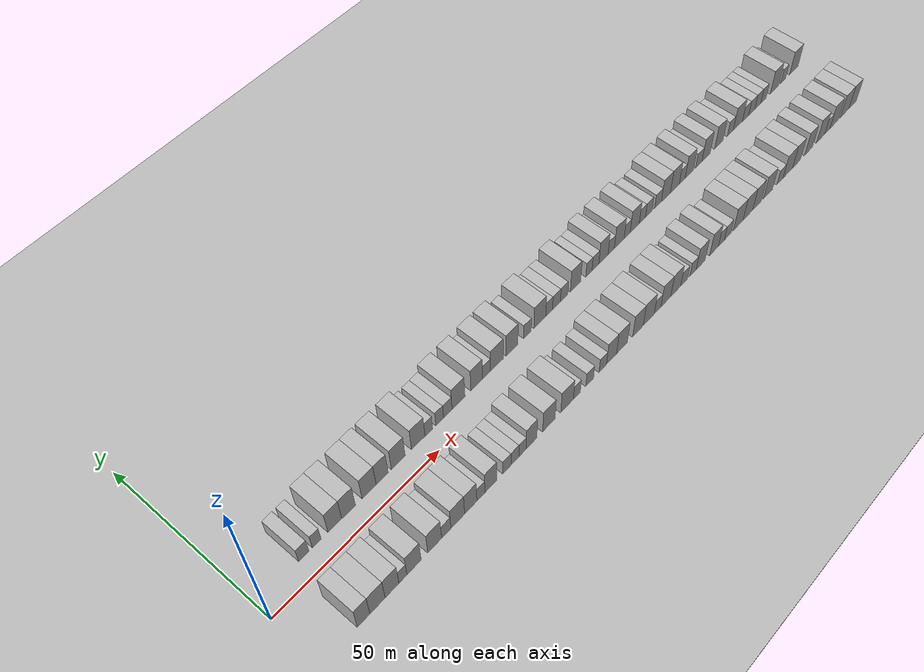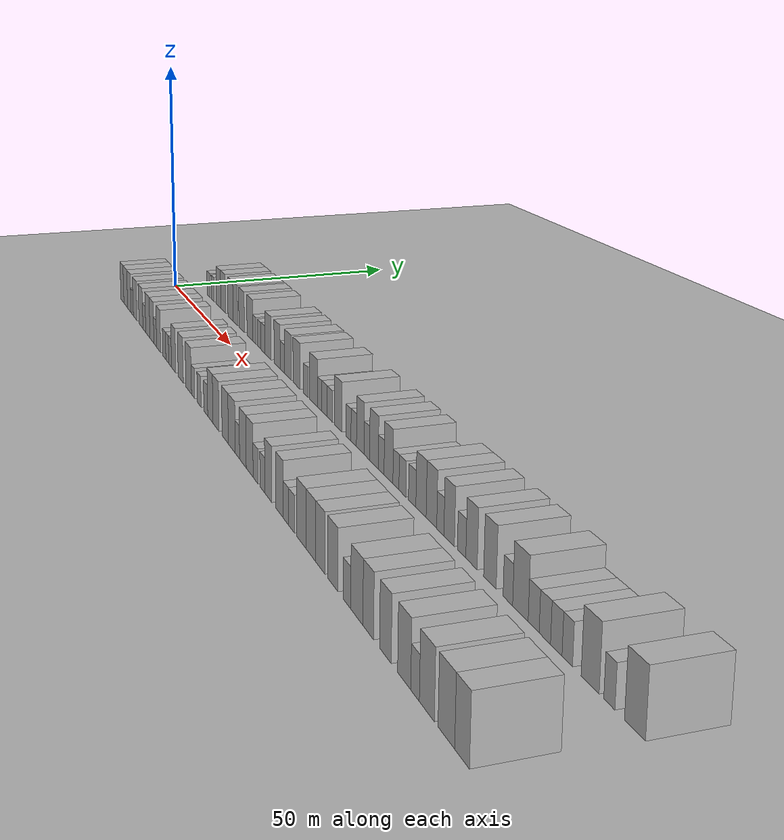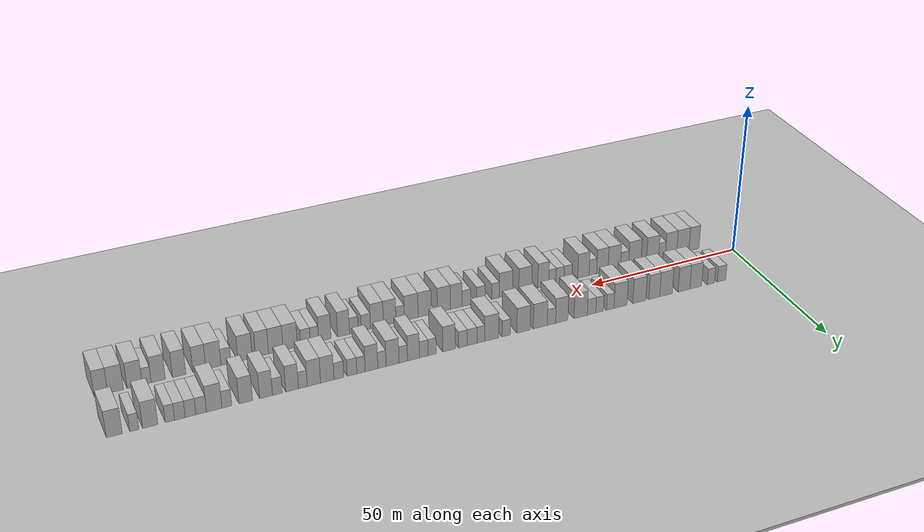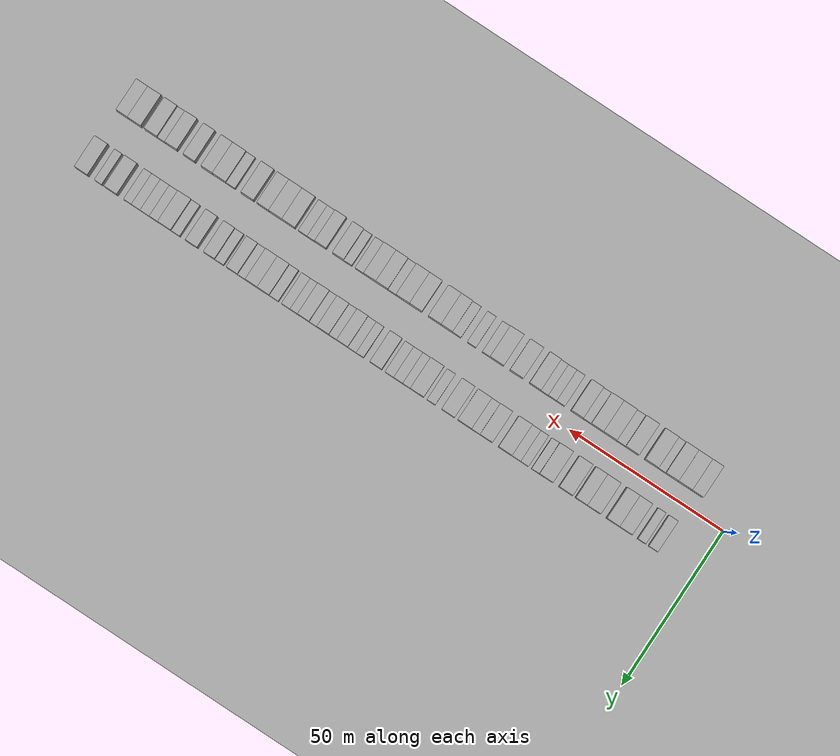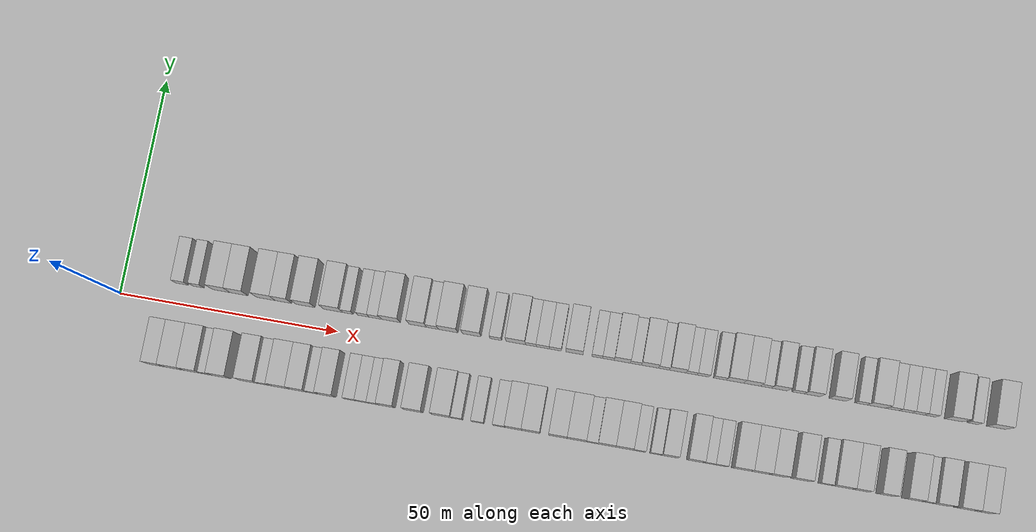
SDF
<?xml version="1.0" encoding="utf-8"?>

<sdf version="1.6">

   <world name="default">

      <gui fullscreen="0">

         <camera name="user_camera">

            <pose>-15 0 4.57585 0 0 0</pose>

            <view_controller>orbit</view_controller>

         </camera>

      </gui>

      <scene>

         <sky>

           <clouds>

             <speed>12</speed>

           </clouds>

         </sky>

         <ambient>0.4 0.4 0.4 1</ambient>

         <background>0.7 0.7 0.7 1</background>

         <shadows>1</shadows>

      </scene>

      <gravity>0 0 -9.8066</gravity>

      <magnetic_field>6e-06 2.3e-05 -4.2e-05</magnetic_field>

      <physics default="0" name="default_physics" type="ode">

         <ode>

            <solver>

               <type>quick</type>

               <iters>10</iters>

               <sor>1.0</sor>

               <use_dynamic_moi_rescaling>0</use_dynamic_moi_rescaling>

            </solver>

            <constraints>

               <cfm>0</cfm>

               <erp>0.2</erp>

               <contact_max_correcting_vel>100</contact_max_correcting_vel>

               <contact_surface_layer>0.001</contact_surface_layer>

            </constraints>

         </ode>

         <max_step_size>0.004</max_step_size>

         <real_time_factor>1</real_time_factor>

         <real_time_update_rate>250</real_time_update_rate>

      </physics>

      <light name="sun" type="directional">

         <cast_shadows>1</cast_shadows>

         <pose>0 0 10 0 0 0</pose>

         <diffuse>0.8 0.8 0.8 1</diffuse>

         <specular>0.2 0.2 0.2 1</specular>

         <attenuation>

            <range>1000</range>

            <constant>0.9</constant>

            <linear>0.01</linear>

            <quadratic>0.001</quadratic>

         </attenuation>

         <direction>-0.5 0.1 -0.9</direction>

      </light>

      <include>

         <name>ground_plane_1</name>

         <uri>model://HANNAS_ground_plane</uri>

         <pose>0 0 0  0 0 0</pose>

      </include>

      <include>

         <name>ground_plane_2</name>

         <uri>model://HANNAS_ground_plane</uri>

         <pose>100 0 0  0 0 0</pose>

      </include>

      <model name="building_1">

         <static>1</static>

         <pose frame="">13.4734 9.5000 0 0.000000 0.000000 1.570796</pose>

         <link name="link">

            <pose frame="">0 0 3.00 0 0 0</pose>

            <collision name="collision">

               <geometry>

                  <box>

                     <size>10.0000 2.9468 6.0000</size>

                  </box>

               </geometry>

               <max_contacts>10</max_contacts>

               <surface>

                  <contact>

                     <ode/>

                  </contact>

                  <bounce/>

                  <friction>

                     <torsional>

                        <ode/>

                     </torsional>

                     <ode/>

                  </friction>

               </surface>

            </collision>

            <visual name="visual">

               <cast_shadows>0</cast_shadows>

               <geometry>

                  <box>

                     <size>10.0000 2.9468 6.0000</size>

                  </box>

               </geometry>

               <material>

                  <script>

                     <uri>model://HANNAS_wall/materials/scripts</uri>

                     <uri>model://HANNAS_wall/materials/textures</uri>

                     <name>vrc/HANNAS_wall</name>

                  </script>

               </material>

            </visual>

            <self_collide>0</self_collide>

            <enable_wind>0</enable_wind>

            <kinematic>0</kinematic>

         </link>

      </model>

      <model name="building_2">

         <static>1</static>

         <pose frame="">17.2123 9.5000 0 0.000000 0.000000 1.570796</pose>

         <link name="link">

            <pose frame="">0 0 3.00 0 0 0</pose>

            <collision name="collision">

               <geometry>

                  <box>

                     <size>10.0000 2.5310 6.0000</size>

                  </box>

               </geometry>

               <max_contacts>10</max_contacts>

               <surface>

                  <contact>

                     <ode/>

                  </contact>

                  <bounce/>

                  <friction>

                     <torsional>

                        <ode/>

                     </torsional>

                     <ode/>

                  </friction>

               </surface>

            </collision>

            <visual name="visual">

               <cast_shadows>0</cast_shadows>

               <geometry>

                  <box>

                     <size>10.0000 2.5310 6.0000</size>

                  </box>

               </geometry>

               <material>

                  <script>

                     <uri>model://HANNAS_wall/materials/scripts</uri>

                     <uri>model://HANNAS_wall/materials/textures</uri>

                     <name>vrc/HANNAS_wall</name>

                  </script>

               </material>

            </visual>

            <self_collide>0</self_collide>

            <enable_wind>0</enable_wind>

            <kinematic>0</kinematic>

         </link>

      </model>

      <model name="building_3">

         <static>1</static>

         <pose frame="">22.5105 9.5000 0 0.000000 0.000000 1.570796</pose>

         <link name="link">

            <pose frame="">0 0 4.50 0 0 0</pose>

            <collision name="collision">

               <geometry>

                  <box>

                     <size>10.0000 4.0656 9.0000</size>

                  </box>

               </geometry>

               <max_contacts>10</max_contacts>

               <surface>

                  <contact>

                     <ode/>

                  </contact>

                  <bounce/>

                  <friction>

                     <torsional>

                        <ode/>

                     </torsional>

                     <ode/>

                  </friction>

               </surface>

            </collision>

            <visual name="visual">

               <cast_shadows>0</cast_shadows>

               <geometry>

                  <box>

                     <size>10.0000 4.0656 9.0000</size>

                  </box>

               </geometry>

               <material>

                  <script>

                     <uri>model://HANNAS_wall/materials/scripts</uri>

                     <uri>model://HANNAS_wall/materials/textures</uri>

                     <name>vrc/HANNAS_wall</name>

                  </script>

               </material>

            </visual>

            <self_collide>0</self_collide>

            <enable_wind>0</enable_wind>

            <kinematic>0</kinematic>

         </link>

      </model>

      <model name="building_4">

         <static>1</static>

         <pose frame="">26.5862 9.5000 0 0.000000 0.000000 1.570796</pose>

         <link name="link">

            <pose frame="">0 0 4.50 0 0 0</pose>

            <collision name="collision">

               <geometry>

                  <box>

                     <size>10.0000 4.0858 9.0000</size>

                  </box>

               </geometry>

               <max_contacts>10</max_contacts>

               <surface>

                  <contact>

                     <ode/>

                  </contact>

                  <bounce/>

                  <friction>

                     <torsional>

                        <ode/>

                     </torsional>

                     <ode/>

                  </friction>

               </surface>

            </collision>

            <visual name="visual">

               <cast_shadows>0</cast_shadows>

               <geometry>

                  <box>

                     <size>10.0000 4.0858 9.0000</size>

                  </box>

               </geometry>

               <material>

                  <script>

                     <uri>model://HANNAS_wall/materials/scripts</uri>

                     <uri>model://HANNAS_wall/materials/textures</uri>

                     <name>vrc/HANNAS_wall</name>

                  </script>

               </material>

            </visual>

            <self_collide>0</self_collide>

            <enable_wind>0</enable_wind>

            <kinematic>0</kinematic>

         </link>

      </model>

      <model name="building_5">

         <static>1</static>

         <pose frame="">32.7871 9.5000 0 0.000000 0.000000 1.570796</pose>

         <link name="link">

            <pose frame="">0 0 4.50 0 0 0</pose>

            <collision name="collision">

               <geometry>

                  <box>

                     <size>10.0000 4.3159 9.0000</size>

                  </box>

               </geometry>

               <max_contacts>10</max_contacts>

               <surface>

                  <contact>

                     <ode/>

                  </contact>

                  <bounce/>

                  <friction>

                     <torsional>

                        <ode/>

                     </torsional>

                     <ode/>

                  </friction>

               </surface>

            </collision>

            <visual name="visual">

               <cast_shadows>0</cast_shadows>

               <geometry>

                  <box>

                     <size>10.0000 4.3159 9.0000</size>

                  </box>

               </geometry>

               <material>

                  <script>

                     <uri>model://HANNAS_wall/materials/scripts</uri>

                     <uri>model://HANNAS_wall/materials/textures</uri>

                     <name>vrc/HANNAS_wall</name>

                  </script>

               </material>

            </visual>

            <self_collide>0</self_collide>

            <enable_wind>0</enable_wind>

            <kinematic>0</kinematic>

         </link>

      </model>

      <model name="building_6">

         <static>1</static>

         <pose frame="">36.8116 9.5000 0 0.000000 0.000000 1.570796</pose>

         <link name="link">

            <pose frame="">0 0 4.50 0 0 0</pose>

            <collision name="collision">

               <geometry>

                  <box>

                     <size>10.0000 3.7332 9.0000</size>

                  </box>

               </geometry>

               <max_contacts>10</max_contacts>

               <surface>

                  <contact>

                     <ode/>

                  </contact>

                  <bounce/>

                  <friction>

                     <torsional>

                        <ode/>

                     </torsional>

                     <ode/>

                  </friction>

               </surface>

            </collision>

            <visual name="visual">

               <cast_shadows>0</cast_shadows>

               <geometry>

                  <box>

                     <size>10.0000 3.7332 9.0000</size>

                  </box>

               </geometry>

               <material>

                  <script>

                     <uri>model://HANNAS_wall/materials/scripts</uri>

                     <uri>model://HANNAS_wall/materials/textures</uri>

                     <name>vrc/HANNAS_wall</name>

                  </script>

               </material>

            </visual>

            <self_collide>0</self_collide>

            <enable_wind>0</enable_wind>

            <kinematic>0</kinematic>

         </link>

      </model>

      <model name="building_7">

         <static>1</static>

         <pose frame="">41.8527 9.5000 0 0.000000 0.000000 1.570796</pose>

         <link name="link">

            <pose frame="">0 0 4.50 0 0 0</pose>

            <collision name="collision">

               <geometry>

                  <box>

                     <size>10.0000 4.3490 9.0000</size>

                  </box>

               </geometry>

               <max_contacts>10</max_contacts>

               <surface>

                  <contact>

                     <ode/>

                  </contact>

                  <bounce/>

                  <friction>

                     <torsional>

                        <ode/>

                     </torsional>

                     <ode/>

                  </friction>

               </surface>

            </collision>

            <visual name="visual">

               <cast_shadows>0</cast_shadows>

               <geometry>

                  <box>

                     <size>10.0000 4.3490 9.0000</size>

                  </box>

               </geometry>

               <material>

                  <script>

                     <uri>model://HANNAS_wall/materials/scripts</uri>

                     <uri>model://HANNAS_wall/materials/textures</uri>

                     <name>vrc/HANNAS_wall</name>

                  </script>

               </material>

            </visual>

            <self_collide>0</self_collide>

            <enable_wind>0</enable_wind>

            <kinematic>0</kinematic>

         </link>

      </model>

      <model name="building_8">

         <static>1</static>

         <pose frame="">48.2076 9.5000 0 0.000000 0.000000 1.570796</pose>

         <link name="link">

            <pose frame="">0 0 4.50 0 0 0</pose>

            <collision name="collision">

               <geometry>

                  <box>

                     <size>10.0000 4.3607 9.0000</size>

                  </box>

               </geometry>

               <max_contacts>10</max_contacts>

               <surface>

                  <contact>

                     <ode/>

                  </contact>

                  <bounce/>

                  <friction>

                     <torsional>

                        <ode/>

                     </torsional>

                     <ode/>

                  </friction>

               </surface>

            </collision>

            <visual name="visual">

               <cast_shadows>0</cast_shadows>

               <geometry>

                  <box>

                     <size>10.0000 4.3607 9.0000</size>

                  </box>

               </geometry>

               <material>

                  <script>

                     <uri>model://HANNAS_wall/materials/scripts</uri>

                     <uri>model://HANNAS_wall/materials/textures</uri>

                     <name>vrc/HANNAS_wall</name>

                  </script>

               </material>

            </visual>

            <self_collide>0</self_collide>

            <enable_wind>0</enable_wind>

            <kinematic>0</kinematic>

         </link>

      </model>

      <model name="building_9">

         <static>1</static>

         <pose frame="">51.6281 9.5000 0 0.000000 0.000000 1.570796</pose>

         <link name="link">

            <pose frame="">0 0 3.00 0 0 0</pose>

            <collision name="collision">

               <geometry>

                  <box>

                     <size>10.0000 2.4804 6.0000</size>

                  </box>

               </geometry>

               <max_contacts>10</max_contacts>

               <surface>

                  <contact>

                     <ode/>

                  </contact>

                  <bounce/>

                  <friction>

                     <torsional>

                        <ode/>

                     </torsional>

                     <ode/>

                  </friction>

               </surface>

            </collision>

            <visual name="visual">

               <cast_shadows>0</cast_shadows>

               <geometry>

                  <box>

                     <size>10.0000 2.4804 6.0000</size>

                  </box>

               </geometry>

               <material>

                  <script>

                     <uri>model://HANNAS_wall/materials/scripts</uri>

                     <uri>model://HANNAS_wall/materials/textures</uri>

                     <name>vrc/HANNAS_wall</name>

                  </script>

               </material>

            </visual>

            <self_collide>0</self_collide>

            <enable_wind>0</enable_wind>

            <kinematic>0</kinematic>

         </link>

      </model>

      <model name="building_10">

         <static>1</static>

         <pose frame="">55.1466 9.5000 0 0.000000 0.000000 1.570796</pose>

         <link name="link">

            <pose frame="">0 0 3.00 0 0 0</pose>

            <collision name="collision">

               <geometry>

                  <box>

                     <size>10.0000 2.5566 6.0000</size>

                  </box>

               </geometry>

               <max_contacts>10</max_contacts>

               <surface>

                  <contact>

                     <ode/>

                  </contact>

                  <bounce/>

                  <friction>

                     <torsional>

                        <ode/>

                     </torsional>

                     <ode/>

                  </friction>

               </surface>

            </collision>

            <visual name="visual">

               <cast_shadows>0</cast_shadows>

               <geometry>

                  <box>

                     <size>10.0000 2.5566 6.0000</size>

                  </box>

               </geometry>

               <material>

                  <script>

                     <uri>model://HANNAS_wall/materials/scripts</uri>

                     <uri>model://HANNAS_wall/materials/textures</uri>

                     <name>vrc/HANNAS_wall</name>

                  </script>

               </material>

            </visual>

            <self_collide>0</self_collide>

            <enable_wind>0</enable_wind>

            <kinematic>0</kinematic>

         </link>

      </model>

      <model name="building_11">

         <static>1</static>

         <pose frame="">57.8463 9.5000 0 0.000000 0.000000 1.570796</pose>

         <link name="link">

            <pose frame="">0 0 3.00 0 0 0</pose>

            <collision name="collision">

               <geometry>

                  <box>

                     <size>10.0000 2.8428 6.0000</size>

                  </box>

               </geometry>

               <max_contacts>10</max_contacts>

               <surface>

                  <contact>

                     <ode/>

                  </contact>

                  <bounce/>

                  <friction>

                     <torsional>

                        <ode/>

                     </torsional>

                     <ode/>

                  </friction>

               </surface>

            </collision>

            <visual name="visual">

               <cast_shadows>0</cast_shadows>

               <geometry>

                  <box>

                     <size>10.0000 2.8428 6.0000</size>

                  </box>

               </geometry>

               <material>

                  <script>

                     <uri>model://HANNAS_wall/materials/scripts</uri>

                     <uri>model://HANNAS_wall/materials/textures</uri>

                     <name>vrc/HANNAS_wall</name>

                  </script>

               </material>

            </visual>

            <self_collide>0</self_collide>

            <enable_wind>0</enable_wind>

            <kinematic>0</kinematic>

         </link>

      </model>

      <model name="building_12">

         <static>1</static>

         <pose frame="">61.4304 9.5000 0 0.000000 0.000000 1.570796</pose>

         <link name="link">

            <pose frame="">0 0 4.50 0 0 0</pose>

            <collision name="collision">

               <geometry>

                  <box>

                     <size>10.0000 4.3254 9.0000</size>

                  </box>

               </geometry>

               <max_contacts>10</max_contacts>

               <surface>

                  <contact>

                     <ode/>

                  </contact>

                  <bounce/>

                  <friction>

                     <torsional>

                        <ode/>

                     </torsional>

                     <ode/>

                  </friction>

               </surface>

            </collision>

            <visual name="visual">

               <cast_shadows>0</cast_shadows>

               <geometry>

                  <box>

                     <size>10.0000 4.3254 9.0000</size>

                  </box>

               </geometry>

               <material>

                  <script>

                     <uri>model://HANNAS_wall/materials/scripts</uri>

                     <uri>model://HANNAS_wall/materials/textures</uri>

                     <name>vrc/HANNAS_wall</name>

                  </script>

               </material>

            </visual>

            <self_collide>0</self_collide>

            <enable_wind>0</enable_wind>

            <kinematic>0</kinematic>

         </link>

      </model>

      <model name="building_13">

         <static>1</static>

         <pose frame="">67.6052 9.5000 0 0.000000 0.000000 1.570796</pose>

         <link name="link">

            <pose frame="">0 0 4.50 0 0 0</pose>

            <collision name="collision">

               <geometry>

                  <box>

                     <size>10.0000 4.0241 9.0000</size>

                  </box>

               </geometry>

               <max_contacts>10</max_contacts>

               <surface>

                  <contact>

                     <ode/>

                  </contact>

                  <bounce/>

                  <friction>

                     <torsional>

                        <ode/>

                     </torsional>

                     <ode/>

                  </friction>

               </surface>

            </collision>

            <visual name="visual">

               <cast_shadows>0</cast_shadows>

               <geometry>

                  <box>

                     <size>10.0000 4.0241 9.0000</size>

                  </box>

               </geometry>

               <material>

                  <script>

                     <uri>model://HANNAS_wall/materials/scripts</uri>

                     <uri>model://HANNAS_wall/materials/textures</uri>

                     <name>vrc/HANNAS_wall</name>

                  </script>

               </material>

            </visual>

            <self_collide>0</self_collide>

            <enable_wind>0</enable_wind>

            <kinematic>0</kinematic>

         </link>

      </model>

      <model name="building_14">

         <static>1</static>

         <pose frame="">70.9708 9.5000 0 0.000000 0.000000 1.570796</pose>

         <link name="link">

            <pose frame="">0 0 3.00 0 0 0</pose>

            <collision name="collision">

               <geometry>

                  <box>

                     <size>10.0000 2.7072 6.0000</size>

                  </box>

               </geometry>

               <max_contacts>10</max_contacts>

               <surface>

                  <contact>

                     <ode/>

                  </contact>

                  <bounce/>

                  <friction>

                     <torsional>

                        <ode/>

                     </torsional>

                     <ode/>

                  </friction>

               </surface>

            </collision>

            <visual name="visual">

               <cast_shadows>0</cast_shadows>

               <geometry>

                  <box>

                     <size>10.0000 2.7072 6.0000</size>

                  </box>

               </geometry>

               <material>

                  <script>

                     <uri>model://HANNAS_wall/materials/scripts</uri>

                     <uri>model://HANNAS_wall/materials/textures</uri>

                     <name>vrc/HANNAS_wall</name>

                  </script>

               </material>

            </visual>

            <self_collide>0</self_collide>

            <enable_wind>0</enable_wind>

            <kinematic>0</kinematic>

         </link>

      </model>

      <model name="building_15">

         <static>1</static>

         <pose frame="">74.5617 9.5000 0 0.000000 0.000000 1.570796</pose>

         <link name="link">

            <pose frame="">0 0 4.50 0 0 0</pose>

            <collision name="collision">

               <geometry>

                  <box>

                     <size>10.0000 4.4746 9.0000</size>

                  </box>

               </geometry>

               <max_contacts>10</max_contacts>

               <surface>

                  <contact>

                     <ode/>

                  </contact>

                  <bounce/>

                  <friction>

                     <torsional>

                        <ode/>

                     </torsional>

                     <ode/>

                  </friction>

               </surface>

            </collision>

            <visual name="visual">

               <cast_shadows>0</cast_shadows>

               <geometry>

                  <box>

                     <size>10.0000 4.4746 9.0000</size>

                  </box>

               </geometry>

               <material>

                  <script>

                     <uri>model://HANNAS_wall/materials/scripts</uri>

                     <uri>model://HANNAS_wall/materials/textures</uri>

                     <name>vrc/HANNAS_wall</name>

                  </script>

               </material>

            </visual>

            <self_collide>0</self_collide>

            <enable_wind>0</enable_wind>

            <kinematic>0</kinematic>

         </link>

      </model>

      <model name="building_16">

         <static>1</static>

         <pose frame="">79.9236 9.5000 0 0.000000 0.000000 1.570796</pose>

         <link name="link">

            <pose frame="">0 0 4.50 0 0 0</pose>

            <collision name="collision">

               <geometry>

                  <box>

                     <size>10.0000 4.2492 9.0000</size>

                  </box>

               </geometry>

               <max_contacts>10</max_contacts>

               <surface>

                  <contact>

                     <ode/>

                  </contact>

                  <bounce/>

                  <friction>

                     <torsional>

                        <ode/>

                     </torsional>

                     <ode/>

                  </friction>

               </surface>

            </collision>

            <visual name="visual">

               <cast_shadows>0</cast_shadows>

               <geometry>

                  <box>

                     <size>10.0000 4.2492 9.0000</size>

                  </box>

               </geometry>

               <material>

                  <script>

                     <uri>model://HANNAS_wall/materials/scripts</uri>

                     <uri>model://HANNAS_wall/materials/textures</uri>

                     <name>vrc/HANNAS_wall</name>

                  </script>

               </material>

            </visual>

            <self_collide>0</self_collide>

            <enable_wind>0</enable_wind>

            <kinematic>0</kinematic>

         </link>

      </model>

      <model name="building_17">

         <static>1</static>

         <pose frame="">85.4104 9.5000 0 0.000000 0.000000 1.570796</pose>

         <link name="link">

            <pose frame="">0 0 3.00 0 0 0</pose>

            <collision name="collision">

               <geometry>

                  <box>

                     <size>10.0000 2.7242 6.0000</size>

                  </box>

               </geometry>

               <max_contacts>10</max_contacts>

               <surface>

                  <contact>

                     <ode/>

                  </contact>

                  <bounce/>

                  <friction>

                     <torsional>

                        <ode/>

                     </torsional>

                     <ode/>

                  </friction>

               </surface>

            </collision>

            <visual name="visual">

               <cast_shadows>0</cast_shadows>

               <geometry>

                  <box>

                     <size>10.0000 2.7242 6.0000</size>

                  </box>

               </geometry>

               <material>

                  <script>

                     <uri>model://HANNAS_wall/materials/scripts</uri>

                     <uri>model://HANNAS_wall/materials/textures</uri>

                     <name>vrc/HANNAS_wall</name>

                  </script>

               </material>

            </visual>

            <self_collide>0</self_collide>

            <enable_wind>0</enable_wind>

            <kinematic>0</kinematic>

         </link>

      </model>

      <model name="building_18">

         <static>1</static>

         <pose frame="">89.9734 9.5000 0 0.000000 0.000000 1.570796</pose>

         <link name="link">

            <pose frame="">0 0 4.50 0 0 0</pose>

            <collision name="collision">

               <geometry>

                  <box>

                     <size>10.0000 4.4019 9.0000</size>

                  </box>

               </geometry>

               <max_contacts>10</max_contacts>

               <surface>

                  <contact>

                     <ode/>

                  </contact>

                  <bounce/>

                  <friction>

                     <torsional>

                        <ode/>

                     </torsional>

                     <ode/>

                  </friction>

               </surface>

            </collision>

            <visual name="visual">

               <cast_shadows>0</cast_shadows>

               <geometry>

                  <box>

                     <size>10.0000 4.4019 9.0000</size>

                  </box>

               </geometry>

               <material>

                  <script>

                     <uri>model://HANNAS_wall/materials/scripts</uri>

                     <uri>model://HANNAS_wall/materials/textures</uri>

                     <name>vrc/HANNAS_wall</name>

                  </script>

               </material>

            </visual>

            <self_collide>0</self_collide>

            <enable_wind>0</enable_wind>

            <kinematic>0</kinematic>

         </link>

      </model>

      <model name="building_19">

         <static>1</static>

         <pose frame="">93.4013 9.5000 0 0.000000 0.000000 1.570796</pose>

         <link name="link">

            <pose frame="">0 0 3.00 0 0 0</pose>

            <collision name="collision">

               <geometry>

                  <box>

                     <size>10.0000 2.4539 6.0000</size>

                  </box>

               </geometry>

               <max_contacts>10</max_contacts>

               <surface>

                  <contact>

                     <ode/>

                  </contact>

                  <bounce/>

                  <friction>

                     <torsional>

                        <ode/>

                     </torsional>

                     <ode/>

                  </friction>

               </surface>

            </collision>

            <visual name="visual">

               <cast_shadows>0</cast_shadows>

               <geometry>

                  <box>

                     <size>10.0000 2.4539 6.0000</size>

                  </box>

               </geometry>

               <material>

                  <script>

                     <uri>model://HANNAS_wall/materials/scripts</uri>

                     <uri>model://HANNAS_wall/materials/textures</uri>

                     <name>vrc/HANNAS_wall</name>

                  </script>

               </material>

            </visual>

            <self_collide>0</self_collide>

            <enable_wind>0</enable_wind>

            <kinematic>0</kinematic>

         </link>

      </model>

      <model name="building_20">

         <static>1</static>

         <pose frame="">96.1024 9.5000 0 0.000000 0.000000 1.570796</pose>

         <link name="link">

            <pose frame="">0 0 3.00 0 0 0</pose>

            <collision name="collision">

               <geometry>

                  <box>

                     <size>10.0000 2.9482 6.0000</size>

                  </box>

               </geometry>

               <max_contacts>10</max_contacts>

               <surface>

                  <contact>

                     <ode/>

                  </contact>

                  <bounce/>

                  <friction>

                     <torsional>

                        <ode/>

                     </torsional>

                     <ode/>

                  </friction>

               </surface>

            </collision>

            <visual name="visual">

               <cast_shadows>0</cast_shadows>

               <geometry>

                  <box>

                     <size>10.0000 2.9482 6.0000</size>

                  </box>

               </geometry>

               <material>

                  <script>

                     <uri>model://HANNAS_wall/materials/scripts</uri>

                     <uri>model://HANNAS_wall/materials/textures</uri>

                     <name>vrc/HANNAS_wall</name>

                  </script>

               </material>

            </visual>

            <self_collide>0</self_collide>

            <enable_wind>0</enable_wind>

            <kinematic>0</kinematic>

         </link>

      </model>

      <model name="building_21">

         <static>1</static>

         <pose frame="">98.9699 9.5000 0 0.000000 0.000000 1.570796</pose>

         <link name="link">

            <pose frame="">0 0 3.00 0 0 0</pose>

            <collision name="collision">

               <geometry>

                  <box>

                     <size>10.0000 2.7868 6.0000</size>

                  </box>

               </geometry>

               <max_contacts>10</max_contacts>

               <surface>

                  <contact>

                     <ode/>

                  </contact>

                  <bounce/>

                  <friction>

                     <torsional>

                        <ode/>

                     </torsional>

                     <ode/>

                  </friction>

               </surface>

            </collision>

            <visual name="visual">

               <cast_shadows>0</cast_shadows>

               <geometry>

                  <box>

                     <size>10.0000 2.7868 6.0000</size>

                  </box>

               </geometry>

               <material>

                  <script>

                     <uri>model://HANNAS_wall/materials/scripts</uri>

                     <uri>model://HANNAS_wall/materials/textures</uri>

                     <name>vrc/HANNAS_wall</name>

                  </script>

               </material>

            </visual>

            <self_collide>0</self_collide>

            <enable_wind>0</enable_wind>

            <kinematic>0</kinematic>

         </link>

      </model>

      <model name="building_22">

         <static>1</static>

         <pose frame="">103.3101 9.5000 0 0.000000 0.000000 1.570796</pose>

         <link name="link">

            <pose frame="">0 0 4.50 0 0 0</pose>

            <collision name="collision">

               <geometry>

                  <box>

                     <size>10.0000 3.8935 9.0000</size>

                  </box>

               </geometry>

               <max_contacts>10</max_contacts>

               <surface>

                  <contact>

                     <ode/>

                  </contact>

                  <bounce/>

                  <friction>

                     <torsional>

                        <ode/>

                     </torsional>

                     <ode/>

                  </friction>

               </surface>

            </collision>

            <visual name="visual">

               <cast_shadows>0</cast_shadows>

               <geometry>

                  <box>

                     <size>10.0000 3.8935 9.0000</size>

                  </box>

               </geometry>

               <material>

                  <script>

                     <uri>model://HANNAS_wall/materials/scripts</uri>

                     <uri>model://HANNAS_wall/materials/textures</uri>

                     <name>vrc/HANNAS_wall</name>

                  </script>

               </material>

            </visual>

            <self_collide>0</self_collide>

            <enable_wind>0</enable_wind>

            <kinematic>0</kinematic>

         </link>

      </model>

      <model name="building_23">

         <static>1</static>

         <pose frame="">108.4847 9.5000 0 0.000000 0.000000 1.570796</pose>

         <link name="link">

            <pose frame="">0 0 3.00 0 0 0</pose>

            <collision name="collision">

               <geometry>

                  <box>

                     <size>10.0000 2.4558 6.0000</size>

                  </box>

               </geometry>

               <max_contacts>10</max_contacts>

               <surface>

                  <contact>

                     <ode/>

                  </contact>

                  <bounce/>

                  <friction>

                     <torsional>

                        <ode/>

                     </torsional>

                     <ode/>

                  </friction>

               </surface>

            </collision>

            <visual name="visual">

               <cast_shadows>0</cast_shadows>

               <geometry>

                  <box>

                     <size>10.0000 2.4558 6.0000</size>

                  </box>

               </geometry>

               <material>

                  <script>

                     <uri>model://HANNAS_wall/materials/scripts</uri>

                     <uri>model://HANNAS_wall/materials/textures</uri>

                     <name>vrc/HANNAS_wall</name>

                  </script>

               </material>

            </visual>

            <self_collide>0</self_collide>

            <enable_wind>0</enable_wind>

            <kinematic>0</kinematic>

         </link>

      </model>

      <model name="building_24">

         <static>1</static>

         <pose frame="">111.0320 9.5000 0 0.000000 0.000000 1.570796</pose>

         <link name="link">

            <pose frame="">0 0 3.00 0 0 0</pose>

            <collision name="collision">

               <geometry>

                  <box>

                     <size>10.0000 2.6387 6.0000</size>

                  </box>

               </geometry>

               <max_contacts>10</max_contacts>

               <surface>

                  <contact>

                     <ode/>

                  </contact>

                  <bounce/>

                  <friction>

                     <torsional>

                        <ode/>

                     </torsional>

                     <ode/>

                  </friction>

               </surface>

            </collision>

            <visual name="visual">

               <cast_shadows>0</cast_shadows>

               <geometry>

                  <box>

                     <size>10.0000 2.6387 6.0000</size>

                  </box>

               </geometry>

               <material>

                  <script>

                     <uri>model://HANNAS_wall/materials/scripts</uri>

                     <uri>model://HANNAS_wall/materials/textures</uri>

                     <name>vrc/HANNAS_wall</name>

                  </script>

               </material>

            </visual>

            <self_collide>0</self_collide>

            <enable_wind>0</enable_wind>

            <kinematic>0</kinematic>

         </link>

      </model>

      <model name="building_25">

         <static>1</static>

         <pose frame="">114.1559 9.5000 0 0.000000 0.000000 1.570796</pose>

         <link name="link">

            <pose frame="">0 0 4.50 0 0 0</pose>

            <collision name="collision">

               <geometry>

                  <box>

                     <size>10.0000 3.6091 9.0000</size>

                  </box>

               </geometry>

               <max_contacts>10</max_contacts>

               <surface>

                  <contact>

                     <ode/>

                  </contact>

                  <bounce/>

                  <friction>

                     <torsional>

                        <ode/>

                     </torsional>

                     <ode/>

                  </friction>

               </surface>

            </collision>

            <visual name="visual">

               <cast_shadows>0</cast_shadows>

               <geometry>

                  <box>

                     <size>10.0000 3.6091 9.0000</size>

                  </box>

               </geometry>

               <material>

                  <script>

                     <uri>model://HANNAS_wall/materials/scripts</uri>

                     <uri>model://HANNAS_wall/materials/textures</uri>

                     <name>vrc/HANNAS_wall</name>

                  </script>

               </material>

            </visual>

            <self_collide>0</self_collide>

            <enable_wind>0</enable_wind>

            <kinematic>0</kinematic>

         </link>

      </model>

      <model name="building_26">

         <static>1</static>

         <pose frame="">117.2297 9.5000 0 0.000000 0.000000 1.570796</pose>

         <link name="link">

            <pose frame="">0 0 3.00 0 0 0</pose>

            <collision name="collision">

               <geometry>

                  <box>

                     <size>10.0000 2.5383 6.0000</size>

                  </box>

               </geometry>

               <max_contacts>10</max_contacts>

               <surface>

                  <contact>

                     <ode/>

                  </contact>

                  <bounce/>

                  <friction>

                     <torsional>

                        <ode/>

                     </torsional>

                     <ode/>

                  </friction>

               </surface>

            </collision>

            <visual name="visual">

               <cast_shadows>0</cast_shadows>

               <geometry>

                  <box>

                     <size>10.0000 2.5383 6.0000</size>

                  </box>

               </geometry>

               <material>

                  <script>

                     <uri>model://HANNAS_wall/materials/scripts</uri>

                     <uri>model://HANNAS_wall/materials/textures</uri>

                     <name>vrc/HANNAS_wall</name>

                  </script>

               </material>

            </visual>

            <self_collide>0</self_collide>

            <enable_wind>0</enable_wind>

            <kinematic>0</kinematic>

         </link>

      </model>

      <model name="building_27">

         <static>1</static>

         <pose frame="">120.4501 9.5000 0 0.000000 0.000000 1.570796</pose>

         <link name="link">

            <pose frame="">0 0 4.50 0 0 0</pose>

            <collision name="collision">

               <geometry>

                  <box>

                     <size>10.0000 3.9025 9.0000</size>

                  </box>

               </geometry>

               <max_contacts>10</max_contacts>

               <surface>

                  <contact>

                     <ode/>

                  </contact>

                  <bounce/>

                  <friction>

                     <torsional>

                        <ode/>

                     </torsional>

                     <ode/>

                  </friction>

               </surface>

            </collision>

            <visual name="visual">

               <cast_shadows>0</cast_shadows>

               <geometry>

                  <box>

                     <size>10.0000 3.9025 9.0000</size>

                  </box>

               </geometry>

               <material>

                  <script>

                     <uri>model://HANNAS_wall/materials/scripts</uri>

                     <uri>model://HANNAS_wall/materials/textures</uri>

                     <name>vrc/HANNAS_wall</name>

                  </script>

               </material>

            </visual>

            <self_collide>0</self_collide>

            <enable_wind>0</enable_wind>

            <kinematic>0</kinematic>

         </link>

      </model>

      <model name="building_28">

         <static>1</static>

         <pose frame="">123.6335 9.5000 0 0.000000 0.000000 1.570796</pose>

         <link name="link">

            <pose frame="">0 0 3.00 0 0 0</pose>

            <collision name="collision">

               <geometry>

                  <box>

                     <size>10.0000 2.4644 6.0000</size>

                  </box>

               </geometry>

               <max_contacts>10</max_contacts>

               <surface>

                  <contact>

                     <ode/>

                  </contact>

                  <bounce/>

                  <friction>

                     <torsional>

                        <ode/>

                     </torsional>

                     <ode/>

                  </friction>

               </surface>

            </collision>

            <visual name="visual">

               <cast_shadows>0</cast_shadows>

               <geometry>

                  <box>

                     <size>10.0000 2.4644 6.0000</size>

                  </box>

               </geometry>

               <material>

                  <script>

                     <uri>model://HANNAS_wall/materials/scripts</uri>

                     <uri>model://HANNAS_wall/materials/textures</uri>

                     <name>vrc/HANNAS_wall</name>

                  </script>

               </material>

            </visual>

            <self_collide>0</self_collide>

            <enable_wind>0</enable_wind>

            <kinematic>0</kinematic>

         </link>

      </model>

      <model name="building_29">

         <static>1</static>

         <pose frame="">126.7385 9.5000 0 0.000000 0.000000 1.570796</pose>

         <link name="link">

            <pose frame="">0 0 4.50 0 0 0</pose>

            <collision name="collision">

               <geometry>

                  <box>

                     <size>10.0000 3.7456 9.0000</size>

                  </box>

               </geometry>

               <max_contacts>10</max_contacts>

               <surface>

                  <contact>

                     <ode/>

                  </contact>

                  <bounce/>

                  <friction>

                     <torsional>

                        <ode/>

                     </torsional>

                     <ode/>

                  </friction>

               </surface>

            </collision>

            <visual name="visual">

               <cast_shadows>0</cast_shadows>

               <geometry>

                  <box>

                     <size>10.0000 3.7456 9.0000</size>

                  </box>

               </geometry>

               <material>

                  <script>

                     <uri>model://HANNAS_wall/materials/scripts</uri>

                     <uri>model://HANNAS_wall/materials/textures</uri>

                     <name>vrc/HANNAS_wall</name>

                  </script>

               </material>

            </visual>

            <self_collide>0</self_collide>

            <enable_wind>0</enable_wind>

            <kinematic>0</kinematic>

         </link>

      </model>

      <model name="building_30">

         <static>1</static>

         <pose frame="">129.8564 9.5000 0 0.000000 0.000000 1.570796</pose>

         <link name="link">

            <pose frame="">0 0 3.00 0 0 0</pose>

            <collision name="collision">

               <geometry>

                  <box>

                     <size>10.0000 2.4900 6.0000</size>

                  </box>

               </geometry>

               <max_contacts>10</max_contacts>

               <surface>

                  <contact>

                     <ode/>

                  </contact>

                  <bounce/>

                  <friction>

                     <torsional>

                        <ode/>

                     </torsional>

                     <ode/>

                  </friction>

               </surface>

            </collision>

            <visual name="visual">

               <cast_shadows>0</cast_shadows>

               <geometry>

                  <box>

                     <size>10.0000 2.4900 6.0000</size>

                  </box>

               </geometry>

               <material>

                  <script>

                     <uri>model://HANNAS_wall/materials/scripts</uri>

                     <uri>model://HANNAS_wall/materials/textures</uri>

                     <name>vrc/HANNAS_wall</name>

                  </script>

               </material>

            </visual>

            <self_collide>0</self_collide>

            <enable_wind>0</enable_wind>

            <kinematic>0</kinematic>

         </link>

      </model>

      <model name="building_31">

         <static>1</static>

         <pose frame="">132.5036 9.5000 0 0.000000 0.000000 1.570796</pose>

         <link name="link">

            <pose frame="">0 0 3.00 0 0 0</pose>

            <collision name="collision">

               <geometry>

                  <box>

                     <size>10.0000 2.8044 6.0000</size>

                  </box>

               </geometry>

               <max_contacts>10</max_contacts>

               <surface>

                  <contact>

                     <ode/>

                  </contact>

                  <bounce/>

                  <friction>

                     <torsional>

                        <ode/>

                     </torsional>

                     <ode/>

                  </friction>

               </surface>

            </collision>

            <visual name="visual">

               <cast_shadows>0</cast_shadows>

               <geometry>

                  <box>

                     <size>10.0000 2.8044 6.0000</size>

                  </box>

               </geometry>

               <material>

                  <script>

                     <uri>model://HANNAS_wall/materials/scripts</uri>

                     <uri>model://HANNAS_wall/materials/textures</uri>

                     <name>vrc/HANNAS_wall</name>

                  </script>

               </material>

            </visual>

            <self_collide>0</self_collide>

            <enable_wind>0</enable_wind>

            <kinematic>0</kinematic>

         </link>

      </model>

      <model name="building_32">

         <static>1</static>

         <pose frame="">136.3526 9.5000 0 0.000000 0.000000 1.570796</pose>

         <link name="link">

            <pose frame="">0 0 3.00 0 0 0</pose>

            <collision name="collision">

               <geometry>

                  <box>

                     <size>10.0000 2.8936 6.0000</size>

                  </box>

               </geometry>

               <max_contacts>10</max_contacts>

               <surface>

                  <contact>

                     <ode/>

                  </contact>

                  <bounce/>

                  <friction>

                     <torsional>

                        <ode/>

                     </torsional>

                     <ode/>

                  </friction>

               </surface>

            </collision>

            <visual name="visual">

               <cast_shadows>0</cast_shadows>

               <geometry>

                  <box>

                     <size>10.0000 2.8936 6.0000</size>

                  </box>

               </geometry>

               <material>

                  <script>

                     <uri>model://HANNAS_wall/materials/scripts</uri>

                     <uri>model://HANNAS_wall/materials/textures</uri>

                     <name>vrc/HANNAS_wall</name>

                  </script>

               </material>

            </visual>

            <self_collide>0</self_collide>

            <enable_wind>0</enable_wind>

            <kinematic>0</kinematic>

         </link>

      </model>

      <model name="building_33">

         <static>1</static>

         <pose frame="">139.7348 9.5000 0 0.000000 0.000000 1.570796</pose>

         <link name="link">

            <pose frame="">0 0 4.50 0 0 0</pose>

            <collision name="collision">

               <geometry>

                  <box>

                     <size>10.0000 3.8708 9.0000</size>

                  </box>

               </geometry>

               <max_contacts>10</max_contacts>

               <surface>

                  <contact>

                     <ode/>

                  </contact>

                  <bounce/>

                  <friction>

                     <torsional>

                        <ode/>

                     </torsional>

                     <ode/>

                  </friction>

               </surface>

            </collision>

            <visual name="visual">

               <cast_shadows>0</cast_shadows>

               <geometry>

                  <box>

                     <size>10.0000 3.8708 9.0000</size>

                  </box>

               </geometry>

               <material>

                  <script>

                     <uri>model://HANNAS_wall/materials/scripts</uri>

                     <uri>model://HANNAS_wall/materials/textures</uri>

                     <name>vrc/HANNAS_wall</name>

                  </script>

               </material>

            </visual>

            <self_collide>0</self_collide>

            <enable_wind>0</enable_wind>

            <kinematic>0</kinematic>

         </link>

      </model>

      <model name="building_34">

         <static>1</static>

         <pose frame="">143.5963 9.5000 0 0.000000 0.000000 1.570796</pose>

         <link name="link">

            <pose frame="">0 0 4.50 0 0 0</pose>

            <collision name="collision">

               <geometry>

                  <box>

                     <size>10.0000 3.8521 9.0000</size>

                  </box>

               </geometry>

               <max_contacts>10</max_contacts>

               <surface>

                  <contact>

                     <ode/>

                  </contact>

                  <bounce/>

                  <friction>

                     <torsional>

                        <ode/>

                     </torsional>

                     <ode/>

                  </friction>

               </surface>

            </collision>

            <visual name="visual">

               <cast_shadows>0</cast_shadows>

               <geometry>

                  <box>

                     <size>10.0000 3.8521 9.0000</size>

                  </box>

               </geometry>

               <material>

                  <script>

                     <uri>model://HANNAS_wall/materials/scripts</uri>

                     <uri>model://HANNAS_wall/materials/textures</uri>

                     <name>vrc/HANNAS_wall</name>

                  </script>

               </material>

            </visual>

            <self_collide>0</self_collide>

            <enable_wind>0</enable_wind>

            <kinematic>0</kinematic>

         </link>

      </model>

      <model name="building_35">

         <static>1</static>

         <pose frame="">146.7884 9.5000 0 0.000000 0.000000 1.570796</pose>

         <link name="link">

            <pose frame="">0 0 3.00 0 0 0</pose>

            <collision name="collision">

               <geometry>

                  <box>

                     <size>10.0000 2.5321 6.0000</size>

                  </box>

               </geometry>

               <max_contacts>10</max_contacts>

               <surface>

                  <contact>

                     <ode/>

                  </contact>

                  <bounce/>

                  <friction>

                     <torsional>

                        <ode/>

                     </torsional>

                     <ode/>

                  </friction>

               </surface>

            </collision>

            <visual name="visual">

               <cast_shadows>0</cast_shadows>

               <geometry>

                  <box>

                     <size>10.0000 2.5321 6.0000</size>

                  </box>

               </geometry>

               <material>

                  <script>

                     <uri>model://HANNAS_wall/materials/scripts</uri>

                     <uri>model://HANNAS_wall/materials/textures</uri>

                     <name>vrc/HANNAS_wall</name>

                  </script>

               </material>

            </visual>

            <self_collide>0</self_collide>

            <enable_wind>0</enable_wind>

            <kinematic>0</kinematic>

         </link>

      </model>

      <model name="building_36">

         <static>1</static>

         <pose frame="">149.8575 9.5000 0 0.000000 0.000000 1.570796</pose>

         <link name="link">

            <pose frame="">0 0 4.50 0 0 0</pose>

            <collision name="collision">

               <geometry>

                  <box>

                     <size>10.0000 3.6062 9.0000</size>

                  </box>

               </geometry>

               <max_contacts>10</max_contacts>

               <surface>

                  <contact>

                     <ode/>

                  </contact>

                  <bounce/>

                  <friction>

                     <torsional>

                        <ode/>

                     </torsional>

                     <ode/>

                  </friction>

               </surface>

            </collision>

            <visual name="visual">

               <cast_shadows>0</cast_shadows>

               <geometry>

                  <box>

                     <size>10.0000 3.6062 9.0000</size>

                  </box>

               </geometry>

               <material>

                  <script>

                     <uri>model://HANNAS_wall/materials/scripts</uri>

                     <uri>model://HANNAS_wall/materials/textures</uri>

                     <name>vrc/HANNAS_wall</name>

                  </script>

               </material>

            </visual>

            <self_collide>0</self_collide>

            <enable_wind>0</enable_wind>

            <kinematic>0</kinematic>

         </link>

      </model>

      <model name="building_37">

         <static>1</static>

         <pose frame="">154.0519 9.5000 0 0.000000 0.000000 1.570796</pose>

         <link name="link">

            <pose frame="">0 0 3.00 0 0 0</pose>

            <collision name="collision">

               <geometry>

                  <box>

                     <size>10.0000 2.7826 6.0000</size>

                  </box>

               </geometry>

               <max_contacts>10</max_contacts>

               <surface>

                  <contact>

                     <ode/>

                  </contact>

                  <bounce/>

                  <friction>

                     <torsional>

                        <ode/>

                     </torsional>

                     <ode/>

                  </friction>

               </surface>

            </collision>

            <visual name="visual">

               <cast_shadows>0</cast_shadows>

               <geometry>

                  <box>

                     <size>10.0000 2.7826 6.0000</size>

                  </box>

               </geometry>

               <material>

                  <script>

                     <uri>model://HANNAS_wall/materials/scripts</uri>

                     <uri>model://HANNAS_wall/materials/textures</uri>

                     <name>vrc/HANNAS_wall</name>

                  </script>

               </material>

            </visual>

            <self_collide>0</self_collide>

            <enable_wind>0</enable_wind>

            <kinematic>0</kinematic>

         </link>

      </model>

      <model name="building_38">

         <static>1</static>

         <pose frame="">157.2575 9.5000 0 0.000000 0.000000 1.570796</pose>

         <link name="link">

            <pose frame="">0 0 4.50 0 0 0</pose>

            <collision name="collision">

               <geometry>

                  <box>

                     <size>10.0000 3.6287 9.0000</size>

                  </box>

               </geometry>

               <max_contacts>10</max_contacts>

               <surface>

                  <contact>

                     <ode/>

                  </contact>

                  <bounce/>

                  <friction>

                     <torsional>

                        <ode/>

                     </torsional>

                     <ode/>

                  </friction>

               </surface>

            </collision>

            <visual name="visual">

               <cast_shadows>0</cast_shadows>

               <geometry>

                  <box>

                     <size>10.0000 3.6287 9.0000</size>

                  </box>

               </geometry>

               <material>

                  <script>

                     <uri>model://HANNAS_wall/materials/scripts</uri>

                     <uri>model://HANNAS_wall/materials/textures</uri>

                     <name>vrc/HANNAS_wall</name>

                  </script>

               </material>

            </visual>

            <self_collide>0</self_collide>

            <enable_wind>0</enable_wind>

            <kinematic>0</kinematic>

         </link>

      </model>

      <model name="building_39">

         <static>1</static>

         <pose frame="">162.9676 9.5000 0 0.000000 0.000000 1.570796</pose>

         <link name="link">

            <pose frame="">0 0 4.50 0 0 0</pose>

            <collision name="collision">

               <geometry>

                  <box>

                     <size>10.0000 3.7915 9.0000</size>

                  </box>

               </geometry>

               <max_contacts>10</max_contacts>

               <surface>

                  <contact>

                     <ode/>

                  </contact>

                  <bounce/>

                  <friction>

                     <torsional>

                        <ode/>

                     </torsional>

                     <ode/>

                  </friction>

               </surface>

            </collision>

            <visual name="visual">

               <cast_shadows>0</cast_shadows>

               <geometry>

                  <box>

                     <size>10.0000 3.7915 9.0000</size>

                  </box>

               </geometry>

               <material>

                  <script>

                     <uri>model://HANNAS_wall/materials/scripts</uri>

                     <uri>model://HANNAS_wall/materials/textures</uri>

                     <name>vrc/HANNAS_wall</name>

                  </script>

               </material>

            </visual>

            <self_collide>0</self_collide>

            <enable_wind>0</enable_wind>

            <kinematic>0</kinematic>

         </link>

      </model>

      <model name="building_40">

         <static>1</static>

         <pose frame="">168.2303 9.5000 0 0.000000 0.000000 1.570796</pose>

         <link name="link">

            <pose frame="">0 0 3.00 0 0 0</pose>

            <collision name="collision">

               <geometry>

                  <box>

                     <size>10.0000 2.7340 6.0000</size>

                  </box>

               </geometry>

               <max_contacts>10</max_contacts>

               <surface>

                  <contact>

                     <ode/>

                  </contact>

                  <bounce/>

                  <friction>

                     <torsional>

                        <ode/>

                     </torsional>

                     <ode/>

                  </friction>

               </surface>

            </collision>

            <visual name="visual">

               <cast_shadows>0</cast_shadows>

               <geometry>

                  <box>

                     <size>10.0000 2.7340 6.0000</size>

                  </box>

               </geometry>

               <material>

                  <script>

                     <uri>model://HANNAS_wall/materials/scripts</uri>

                     <uri>model://HANNAS_wall/materials/textures</uri>

                     <name>vrc/HANNAS_wall</name>

                  </script>

               </material>

            </visual>

            <self_collide>0</self_collide>

            <enable_wind>0</enable_wind>

            <kinematic>0</kinematic>

         </link>

      </model>

      <model name="building_41">

         <static>1</static>

         <pose frame="">171.7309 9.5000 0 0.000000 0.000000 1.570796</pose>

         <link name="link">

            <pose frame="">0 0 4.50 0 0 0</pose>

            <collision name="collision">

               <geometry>

                  <box>

                     <size>10.0000 4.2672 9.0000</size>

                  </box>

               </geometry>

               <max_contacts>10</max_contacts>

               <surface>

                  <contact>

                     <ode/>

                  </contact>

                  <bounce/>

                  <friction>

                     <torsional>

                        <ode/>

                     </torsional>

                     <ode/>

                  </friction>

               </surface>

            </collision>

            <visual name="visual">

               <cast_shadows>0</cast_shadows>

               <geometry>

                  <box>

                     <size>10.0000 4.2672 9.0000</size>

                  </box>

               </geometry>

               <material>

                  <script>

                     <uri>model://HANNAS_wall/materials/scripts</uri>

                     <uri>model://HANNAS_wall/materials/textures</uri>

                     <name>vrc/HANNAS_wall</name>

                  </script>

               </material>

            </visual>

            <self_collide>0</self_collide>

            <enable_wind>0</enable_wind>

            <kinematic>0</kinematic>

         </link>

      </model>

      <model name="building_42">

         <static>1</static>

         <pose frame="">175.3199 9.5000 0 0.000000 0.000000 1.570796</pose>

         <link name="link">

            <pose frame="">0 0 3.00 0 0 0</pose>

            <collision name="collision">

               <geometry>

                  <box>

                     <size>10.0000 2.9108 6.0000</size>

                  </box>

               </geometry>

               <max_contacts>10</max_contacts>

               <surface>

                  <contact>

                     <ode/>

                  </contact>

                  <bounce/>

                  <friction>

                     <torsional>

                        <ode/>

                     </torsional>

                     <ode/>

                  </friction>

               </surface>

            </collision>

            <visual name="visual">

               <cast_shadows>0</cast_shadows>

               <geometry>

                  <box>

                     <size>10.0000 2.9108 6.0000</size>

                  </box>

               </geometry>

               <material>

                  <script>

                     <uri>model://HANNAS_wall/materials/scripts</uri>

                     <uri>model://HANNAS_wall/materials/textures</uri>

                     <name>vrc/HANNAS_wall</name>

                  </script>

               </material>

            </visual>

            <self_collide>0</self_collide>

            <enable_wind>0</enable_wind>

            <kinematic>0</kinematic>

         </link>

      </model>

      <model name="building_43">

         <static>1</static>

         <pose frame="">178.2325 9.5000 0 0.000000 0.000000 1.570796</pose>

         <link name="link">

            <pose frame="">0 0 3.00 0 0 0</pose>

            <collision name="collision">

               <geometry>

                  <box>

                     <size>10.0000 2.9144 6.0000</size>

                  </box>

               </geometry>

               <max_contacts>10</max_contacts>

               <surface>

                  <contact>

                     <ode/>

                  </contact>

                  <bounce/>

                  <friction>

                     <torsional>

                        <ode/>

                     </torsional>

                     <ode/>

                  </friction>

               </surface>

            </collision>

            <visual name="visual">

               <cast_shadows>0</cast_shadows>

               <geometry>

                  <box>

                     <size>10.0000 2.9144 6.0000</size>

                  </box>

               </geometry>

               <material>

                  <script>

                     <uri>model://HANNAS_wall/materials/scripts</uri>

                     <uri>model://HANNAS_wall/materials/textures</uri>

                     <name>vrc/HANNAS_wall</name>

                  </script>

               </material>

            </visual>

            <self_collide>0</self_collide>

            <enable_wind>0</enable_wind>

            <kinematic>0</kinematic>

         </link>

      </model>

      <model name="building_44">

         <static>1</static>

         <pose frame="">181.1167 9.5000 0 0.000000 0.000000 1.570796</pose>

         <link name="link">

            <pose frame="">0 0 3.00 0 0 0</pose>

            <collision name="collision">

               <geometry>

                  <box>

                     <size>10.0000 2.8540 6.0000</size>

                  </box>

               </geometry>

               <max_contacts>10</max_contacts>

               <surface>

                  <contact>

                     <ode/>

                  </contact>

                  <bounce/>

                  <friction>

                     <torsional>

                        <ode/>

                     </torsional>

                     <ode/>

                  </friction>

               </surface>

            </collision>

            <visual name="visual">

               <cast_shadows>0</cast_shadows>

               <geometry>

                  <box>

                     <size>10.0000 2.8540 6.0000</size>

                  </box>

               </geometry>

               <material>

                  <script>

                     <uri>model://HANNAS_wall/materials/scripts</uri>

                     <uri>model://HANNAS_wall/materials/textures</uri>

                     <name>vrc/HANNAS_wall</name>

                  </script>

               </material>

            </visual>

            <self_collide>0</self_collide>

            <enable_wind>0</enable_wind>

            <kinematic>0</kinematic>

         </link>

      </model>

      <model name="building_45">

         <static>1</static>

         <pose frame="">183.8082 9.5000 0 0.000000 0.000000 1.570796</pose>

         <link name="link">

            <pose frame="">0 0 3.00 0 0 0</pose>

            <collision name="collision">

               <geometry>

                  <box>

                     <size>10.0000 2.5291 6.0000</size>

                  </box>

               </geometry>

               <max_contacts>10</max_contacts>

               <surface>

                  <contact>

                     <ode/>

                  </contact>

                  <bounce/>

                  <friction>

                     <torsional>

                        <ode/>

                     </torsional>

                     <ode/>

                  </friction>

               </surface>

            </collision>

            <visual name="visual">

               <cast_shadows>0</cast_shadows>

               <geometry>

                  <box>

                     <size>10.0000 2.5291 6.0000</size>

                  </box>

               </geometry>

               <material>

                  <script>

                     <uri>model://HANNAS_wall/materials/scripts</uri>

                     <uri>model://HANNAS_wall/materials/textures</uri>

                     <name>vrc/HANNAS_wall</name>

                  </script>

               </material>

            </visual>

            <self_collide>0</self_collide>

            <enable_wind>0</enable_wind>

            <kinematic>0</kinematic>

         </link>

      </model>

      <model name="building_46">

         <static>1</static>

         <pose frame="">189.1206 9.5000 0 0.000000 0.000000 1.570796</pose>

         <link name="link">

            <pose frame="">0 0 4.50 0 0 0</pose>

            <collision name="collision">

               <geometry>

                  <box>

                     <size>10.0000 4.0956 9.0000</size>

                  </box>

               </geometry>

               <max_contacts>10</max_contacts>

               <surface>

                  <contact>

                     <ode/>

                  </contact>

                  <bounce/>

                  <friction>

                     <torsional>

                        <ode/>

                     </torsional>

                     <ode/>

                  </friction>

               </surface>

            </collision>

            <visual name="visual">

               <cast_shadows>0</cast_shadows>

               <geometry>

                  <box>

                     <size>10.0000 4.0956 9.0000</size>

                  </box>

               </geometry>

               <material>

                  <script>

                     <uri>model://HANNAS_wall/materials/scripts</uri>

                     <uri>model://HANNAS_wall/materials/textures</uri>

                     <name>vrc/HANNAS_wall</name>

                  </script>

               </material>

            </visual>

            <self_collide>0</self_collide>

            <enable_wind>0</enable_wind>

            <kinematic>0</kinematic>

         </link>

      </model>

      <model name="building_47">

         <static>1</static>

         <pose frame="">193.3702 9.5000 0 0.000000 0.000000 1.570796</pose>

         <link name="link">

            <pose frame="">0 0 3.00 0 0 0</pose>

            <collision name="collision">

               <geometry>

                  <box>

                     <size>10.0000 2.4036 6.0000</size>

                  </box>

               </geometry>

               <max_contacts>10</max_contacts>

               <surface>

                  <contact>

                     <ode/>

                  </contact>

                  <bounce/>

                  <friction>

                     <torsional>

                        <ode/>

                     </torsional>

                     <ode/>

                  </friction>

               </surface>

            </collision>

            <visual name="visual">

               <cast_shadows>0</cast_shadows>

               <geometry>

                  <box>

                     <size>10.0000 2.4036 6.0000</size>

                  </box>

               </geometry>

               <material>

                  <script>

                     <uri>model://HANNAS_wall/materials/scripts</uri>

                     <uri>model://HANNAS_wall/materials/textures</uri>

                     <name>vrc/HANNAS_wall</name>

                  </script>

               </material>

            </visual>

            <self_collide>0</self_collide>

            <enable_wind>0</enable_wind>

            <kinematic>0</kinematic>

         </link>

      </model>

      <model name="building_48">

         <static>1</static>

         <pose frame="">198.6882 9.5000 0 0.000000 0.000000 1.570796</pose>

         <link name="link">

            <pose frame="">0 0 4.50 0 0 0</pose>

            <collision name="collision">

               <geometry>

                  <box>

                     <size>10.0000 4.2324 9.0000</size>

                  </box>

               </geometry>

               <max_contacts>10</max_contacts>

               <surface>

                  <contact>

                     <ode/>

                  </contact>

                  <bounce/>

                  <friction>

                     <torsional>

                        <ode/>

                     </torsional>

                     <ode/>

                  </friction>

               </surface>

            </collision>

            <visual name="visual">

               <cast_shadows>0</cast_shadows>

               <geometry>

                  <box>

                     <size>10.0000 4.2324 9.0000</size>

                  </box>

               </geometry>

               <material>

                  <script>

                     <uri>model://HANNAS_wall/materials/scripts</uri>

                     <uri>model://HANNAS_wall/materials/textures</uri>

                     <name>vrc/HANNAS_wall</name>

                  </script>

               </material>

            </visual>

            <self_collide>0</self_collide>

            <enable_wind>0</enable_wind>

            <kinematic>0</kinematic>

         </link>

      </model>

      <model name="building_49">

         <static>1</static>

         <pose frame="">11.8109 -9.5000 0 0.000000 0.000000 1.570796</pose>

         <link name="link">

            <pose frame="">0 0 4.50 0 0 0</pose>

            <collision name="collision">

               <geometry>

                  <box>

                     <size>10.0000 3.6219 9.0000</size>

                  </box>

               </geometry>

               <max_contacts>10</max_contacts>

               <surface>

                  <contact>

                     <ode/>

                  </contact>

                  <bounce/>

                  <friction>

                     <torsional>

                        <ode/>

                     </torsional>

                     <ode/>

                  </friction>

               </surface>

            </collision>

            <visual name="visual">

               <cast_shadows>0</cast_shadows>

               <geometry>

                  <box>

                     <size>10.0000 3.6219 9.0000</size>

                  </box>

               </geometry>

               <material>

                  <script>

                     <uri>model://HANNAS_wall/materials/scripts</uri>

                     <uri>model://HANNAS_wall/materials/textures</uri>

                     <name>vrc/HANNAS_wall</name>

                  </script>

               </material>

            </visual>

            <self_collide>0</self_collide>

            <enable_wind>0</enable_wind>

            <kinematic>0</kinematic>

         </link>

      </model>

      <model name="building_50">

         <static>1</static>

         <pose frame="">15.8263 -9.5000 0 0.000000 0.000000 1.570796</pose>

         <link name="link">

            <pose frame="">0 0 4.50 0 0 0</pose>

            <collision name="collision">

               <geometry>

                  <box>

                     <size>10.0000 4.4089 9.0000</size>

                  </box>

               </geometry>

               <max_contacts>10</max_contacts>

               <surface>

                  <contact>

                     <ode/>

                  </contact>

                  <bounce/>

                  <friction>

                     <torsional>

                        <ode/>

                     </torsional>

                     <ode/>

                  </friction>

               </surface>

            </collision>

            <visual name="visual">

               <cast_shadows>0</cast_shadows>

               <geometry>

                  <box>

                     <size>10.0000 4.4089 9.0000</size>

                  </box>

               </geometry>

               <material>

                  <script>

                     <uri>model://HANNAS_wall/materials/scripts</uri>

                     <uri>model://HANNAS_wall/materials/textures</uri>

                     <name>vrc/HANNAS_wall</name>

                  </script>

               </material>

            </visual>

            <self_collide>0</self_collide>

            <enable_wind>0</enable_wind>

            <kinematic>0</kinematic>

         </link>

      </model>

      <model name="building_51">

         <static>1</static>

         <pose frame="">20.0552 -9.5000 0 0.000000 0.000000 1.570796</pose>

         <link name="link">

            <pose frame="">0 0 4.50 0 0 0</pose>

            <collision name="collision">

               <geometry>

                  <box>

                     <size>10.0000 4.0487 9.0000</size>

                  </box>

               </geometry>

               <max_contacts>10</max_contacts>

               <surface>

                  <contact>

                     <ode/>

                  </contact>

                  <bounce/>

                  <friction>

                     <torsional>

                        <ode/>

                     </torsional>

                     <ode/>

                  </friction>

               </surface>

            </collision>

            <visual name="visual">

               <cast_shadows>0</cast_shadows>

               <geometry>

                  <box>

                     <size>10.0000 4.0487 9.0000</size>

                  </box>

               </geometry>

               <material>

                  <script>

                     <uri>model://HANNAS_wall/materials/scripts</uri>

                     <uri>model://HANNAS_wall/materials/textures</uri>

                     <name>vrc/HANNAS_wall</name>

                  </script>

               </material>

            </visual>

            <self_collide>0</self_collide>

            <enable_wind>0</enable_wind>

            <kinematic>0</kinematic>

         </link>

      </model>

      <model name="building_52">

         <static>1</static>

         <pose frame="">23.2805 -9.5000 0 0.000000 0.000000 1.570796</pose>

         <link name="link">

            <pose frame="">0 0 3.00 0 0 0</pose>

            <collision name="collision">

               <geometry>

                  <box>

                     <size>10.0000 2.4020 6.0000</size>

                  </box>

               </geometry>

               <max_contacts>10</max_contacts>

               <surface>

                  <contact>

                     <ode/>

                  </contact>

                  <bounce/>

                  <friction>

                     <torsional>

                        <ode/>

                     </torsional>

                     <ode/>

                  </friction>

               </surface>

            </collision>

            <visual name="visual">

               <cast_shadows>0</cast_shadows>

               <geometry>

                  <box>

                     <size>10.0000 2.4020 6.0000</size>

                  </box>

               </geometry>

               <material>

                  <script>

                     <uri>model://HANNAS_wall/materials/scripts</uri>

                     <uri>model://HANNAS_wall/materials/textures</uri>

                     <name>vrc/HANNAS_wall</name>

                  </script>

               </material>

            </visual>

            <self_collide>0</self_collide>

            <enable_wind>0</enable_wind>

            <kinematic>0</kinematic>

         </link>

      </model>

      <model name="building_53">

         <static>1</static>

         <pose frame="">26.6214 -9.5000 0 0.000000 0.000000 1.570796</pose>

         <link name="link">

            <pose frame="">0 0 4.50 0 0 0</pose>

            <collision name="collision">

               <geometry>

                  <box>

                     <size>10.0000 4.2799 9.0000</size>

                  </box>

               </geometry>

               <max_contacts>10</max_contacts>

               <surface>

                  <contact>

                     <ode/>

                  </contact>

                  <bounce/>

                  <friction>

                     <torsional>

                        <ode/>

                     </torsional>

                     <ode/>

                  </friction>

               </surface>

            </collision>

            <visual name="visual">

               <cast_shadows>0</cast_shadows>

               <geometry>

                  <box>

                     <size>10.0000 4.2799 9.0000</size>

                  </box>

               </geometry>

               <material>

                  <script>

                     <uri>model://HANNAS_wall/materials/scripts</uri>

                     <uri>model://HANNAS_wall/materials/textures</uri>

                     <name>vrc/HANNAS_wall</name>

                  </script>

               </material>

            </visual>

            <self_collide>0</self_collide>

            <enable_wind>0</enable_wind>

            <kinematic>0</kinematic>

         </link>

      </model>

      <model name="building_54">

         <static>1</static>

         <pose frame="">32.8958 -9.5000 0 0.000000 0.000000 1.570796</pose>

         <link name="link">

            <pose frame="">0 0 4.50 0 0 0</pose>

            <collision name="collision">

               <geometry>

                  <box>

                     <size>10.0000 4.2688 9.0000</size>

                  </box>

               </geometry>

               <max_contacts>10</max_contacts>

               <surface>

                  <contact>

                     <ode/>

                  </contact>

                  <bounce/>

                  <friction>

                     <torsional>

                        <ode/>

                     </torsional>

                     <ode/>

                  </friction>

               </surface>

            </collision>

            <visual name="visual">

               <cast_shadows>0</cast_shadows>

               <geometry>

                  <box>

                     <size>10.0000 4.2688 9.0000</size>

                  </box>

               </geometry>

               <material>

                  <script>

                     <uri>model://HANNAS_wall/materials/scripts</uri>

                     <uri>model://HANNAS_wall/materials/textures</uri>

                     <name>vrc/HANNAS_wall</name>

                  </script>

               </material>

            </visual>

            <self_collide>0</self_collide>

            <enable_wind>0</enable_wind>

            <kinematic>0</kinematic>

         </link>

      </model>

      <model name="building_55">

         <static>1</static>

         <pose frame="">36.4688 -9.5000 0 0.000000 0.000000 1.570796</pose>

         <link name="link">

            <pose frame="">0 0 3.00 0 0 0</pose>

            <collision name="collision">

               <geometry>

                  <box>

                     <size>10.0000 2.8772 6.0000</size>

                  </box>

               </geometry>

               <max_contacts>10</max_contacts>

               <surface>

                  <contact>

                     <ode/>

                  </contact>

                  <bounce/>

                  <friction>

                     <torsional>

                        <ode/>

                     </torsional>

                     <ode/>

                  </friction>

               </surface>

            </collision>

            <visual name="visual">

               <cast_shadows>0</cast_shadows>

               <geometry>

                  <box>

                     <size>10.0000 2.8772 6.0000</size>

                  </box>

               </geometry>

               <material>

                  <script>

                     <uri>model://HANNAS_wall/materials/scripts</uri>

                     <uri>model://HANNAS_wall/materials/textures</uri>

                     <name>vrc/HANNAS_wall</name>

                  </script>

               </material>

            </visual>

            <self_collide>0</self_collide>

            <enable_wind>0</enable_wind>

            <kinematic>0</kinematic>

         </link>

      </model>

      <model name="building_56">

         <static>1</static>

         <pose frame="">40.0684 -9.5000 0 0.000000 0.000000 1.570796</pose>

         <link name="link">

            <pose frame="">0 0 4.50 0 0 0</pose>

            <collision name="collision">

               <geometry>

                  <box>

                     <size>10.0000 4.3221 9.0000</size>

                  </box>

               </geometry>

               <max_contacts>10</max_contacts>

               <surface>

                  <contact>

                     <ode/>

                  </contact>

                  <bounce/>

                  <friction>

                     <torsional>

                        <ode/>

                     </torsional>

                     <ode/>

                  </friction>

               </surface>

            </collision>

            <visual name="visual">

               <cast_shadows>0</cast_shadows>

               <geometry>

                  <box>

                     <size>10.0000 4.3221 9.0000</size>

                  </box>

               </geometry>

               <material>

                  <script>

                     <uri>model://HANNAS_wall/materials/scripts</uri>

                     <uri>model://HANNAS_wall/materials/textures</uri>

                     <name>vrc/HANNAS_wall</name>

                  </script>

               </material>

            </visual>

            <self_collide>0</self_collide>

            <enable_wind>0</enable_wind>

            <kinematic>0</kinematic>

         </link>

      </model>

      <model name="building_57">

         <static>1</static>

         <pose frame="">44.1926 -9.5000 0 0.000000 0.000000 1.570796</pose>

         <link name="link">

            <pose frame="">0 0 4.50 0 0 0</pose>

            <collision name="collision">

               <geometry>

                  <box>

                     <size>10.0000 3.9262 9.0000</size>

                  </box>

               </geometry>

               <max_contacts>10</max_contacts>

               <surface>

                  <contact>

                     <ode/>

                  </contact>

                  <bounce/>

                  <friction>

                     <torsional>

                        <ode/>

                     </torsional>

                     <ode/>

                  </friction>

               </surface>

            </collision>

            <visual name="visual">

               <cast_shadows>0</cast_shadows>

               <geometry>

                  <box>

                     <size>10.0000 3.9262 9.0000</size>

                  </box>

               </geometry>

               <material>

                  <script>

                     <uri>model://HANNAS_wall/materials/scripts</uri>

                     <uri>model://HANNAS_wall/materials/textures</uri>

                     <name>vrc/HANNAS_wall</name>

                  </script>

               </material>

            </visual>

            <self_collide>0</self_collide>

            <enable_wind>0</enable_wind>

            <kinematic>0</kinematic>

         </link>

      </model>

      <model name="building_58">

         <static>1</static>

         <pose frame="">47.4564 -9.5000 0 0.000000 0.000000 1.570796</pose>

         <link name="link">

            <pose frame="">0 0 3.00 0 0 0</pose>

            <collision name="collision">

               <geometry>

                  <box>

                     <size>10.0000 2.6013 6.0000</size>

                  </box>

               </geometry>

               <max_contacts>10</max_contacts>

               <surface>

                  <contact>

                     <ode/>

                  </contact>

                  <bounce/>

                  <friction>

                     <torsional>

                        <ode/>

                     </torsional>

                     <ode/>

                  </friction>

               </surface>

            </collision>

            <visual name="visual">

               <cast_shadows>0</cast_shadows>

               <geometry>

                  <box>

                     <size>10.0000 2.6013 6.0000</size>

                  </box>

               </geometry>

               <material>

                  <script>

                     <uri>model://HANNAS_wall/materials/scripts</uri>

                     <uri>model://HANNAS_wall/materials/textures</uri>

                     <name>vrc/HANNAS_wall</name>

                  </script>

               </material>

            </visual>

            <self_collide>0</self_collide>

            <enable_wind>0</enable_wind>

            <kinematic>0</kinematic>

         </link>

      </model>

      <model name="building_59">

         <static>1</static>

         <pose frame="">50.6944 -9.5000 0 0.000000 0.000000 1.570796</pose>

         <link name="link">

            <pose frame="">0 0 4.50 0 0 0</pose>

            <collision name="collision">

               <geometry>

                  <box>

                     <size>10.0000 3.8748 9.0000</size>

                  </box>

               </geometry>

               <max_contacts>10</max_contacts>

               <surface>

                  <contact>

                     <ode/>

                  </contact>

                  <bounce/>

                  <friction>

                     <torsional>

                        <ode/>

                     </torsional>

                     <ode/>

                  </friction>

               </surface>

            </collision>

            <visual name="visual">

               <cast_shadows>0</cast_shadows>

               <geometry>

                  <box>

                     <size>10.0000 3.8748 9.0000</size>

                  </box>

               </geometry>

               <material>

                  <script>

                     <uri>model://HANNAS_wall/materials/scripts</uri>

                     <uri>model://HANNAS_wall/materials/textures</uri>

                     <name>vrc/HANNAS_wall</name>

                  </script>

               </material>

            </visual>

            <self_collide>0</self_collide>

            <enable_wind>0</enable_wind>

            <kinematic>0</kinematic>

         </link>

      </model>

      <model name="building_60">

         <static>1</static>

         <pose frame="">55.9713 -9.5000 0 0.000000 0.000000 1.570796</pose>

         <link name="link">

            <pose frame="">0 0 3.00 0 0 0</pose>

            <collision name="collision">

               <geometry>

                  <box>

                     <size>10.0000 2.6790 6.0000</size>

                  </box>

               </geometry>

               <max_contacts>10</max_contacts>

               <surface>

                  <contact>

                     <ode/>

                  </contact>

                  <bounce/>

                  <friction>

                     <torsional>

                        <ode/>

                     </torsional>

                     <ode/>

                  </friction>

               </surface>

            </collision>

            <visual name="visual">

               <cast_shadows>0</cast_shadows>

               <geometry>

                  <box>

                     <size>10.0000 2.6790 6.0000</size>

                  </box>

               </geometry>

               <material>

                  <script>

                     <uri>model://HANNAS_wall/materials/scripts</uri>

                     <uri>model://HANNAS_wall/materials/textures</uri>

                     <name>vrc/HANNAS_wall</name>

                  </script>

               </material>

            </visual>

            <self_collide>0</self_collide>

            <enable_wind>0</enable_wind>

            <kinematic>0</kinematic>

         </link>

      </model>

      <model name="building_61">

         <static>1</static>

         <pose frame="">58.6666 -9.5000 0 0.000000 0.000000 1.570796</pose>

         <link name="link">

            <pose frame="">0 0 3.00 0 0 0</pose>

            <collision name="collision">

               <geometry>

                  <box>

                     <size>10.0000 2.7116 6.0000</size>

                  </box>

               </geometry>

               <max_contacts>10</max_contacts>

               <surface>

                  <contact>

                     <ode/>

                  </contact>

                  <bounce/>

                  <friction>

                     <torsional>

                        <ode/>

                     </torsional>

                     <ode/>

                  </friction>

               </surface>

            </collision>

            <visual name="visual">

               <cast_shadows>0</cast_shadows>

               <geometry>

                  <box>

                     <size>10.0000 2.7116 6.0000</size>

                  </box>

               </geometry>

               <material>

                  <script>

                     <uri>model://HANNAS_wall/materials/scripts</uri>

                     <uri>model://HANNAS_wall/materials/textures</uri>

                     <name>vrc/HANNAS_wall</name>

                  </script>

               </material>

            </visual>

            <self_collide>0</self_collide>

            <enable_wind>0</enable_wind>

            <kinematic>0</kinematic>

         </link>

      </model>

      <model name="building_62">

         <static>1</static>

         <pose frame="">61.2330 -9.5000 0 0.000000 0.000000 1.570796</pose>

         <link name="link">

            <pose frame="">0 0 3.00 0 0 0</pose>

            <collision name="collision">

               <geometry>

                  <box>

                     <size>10.0000 2.4212 6.0000</size>

                  </box>

               </geometry>

               <max_contacts>10</max_contacts>

               <surface>

                  <contact>

                     <ode/>

                  </contact>

                  <bounce/>

                  <friction>

                     <torsional>

                        <ode/>

                     </torsional>

                     <ode/>

                  </friction>

               </surface>

            </collision>

            <visual name="visual">

               <cast_shadows>0</cast_shadows>

               <geometry>

                  <box>

                     <size>10.0000 2.4212 6.0000</size>

                  </box>

               </geometry>

               <material>

                  <script>

                     <uri>model://HANNAS_wall/materials/scripts</uri>

                     <uri>model://HANNAS_wall/materials/textures</uri>

                     <name>vrc/HANNAS_wall</name>

                  </script>

               </material>

            </visual>

            <self_collide>0</self_collide>

            <enable_wind>0</enable_wind>

            <kinematic>0</kinematic>

         </link>

      </model>

      <model name="building_63">

         <static>1</static>

         <pose frame="">64.2825 -9.5000 0 0.000000 0.000000 1.570796</pose>

         <link name="link">

            <pose frame="">0 0 4.50 0 0 0</pose>

            <collision name="collision">

               <geometry>

                  <box>

                     <size>10.0000 3.6779 9.0000</size>

                  </box>

               </geometry>

               <max_contacts>10</max_contacts>

               <surface>

                  <contact>

                     <ode/>

                  </contact>

                  <bounce/>

                  <friction>

                     <torsional>

                        <ode/>

                     </torsional>

                     <ode/>

                  </friction>

               </surface>

            </collision>

            <visual name="visual">

               <cast_shadows>0</cast_shadows>

               <geometry>

                  <box>

                     <size>10.0000 3.6779 9.0000</size>

                  </box>

               </geometry>

               <material>

                  <script>

                     <uri>model://HANNAS_wall/materials/scripts</uri>

                     <uri>model://HANNAS_wall/materials/textures</uri>

                     <name>vrc/HANNAS_wall</name>

                  </script>

               </material>

            </visual>

            <self_collide>0</self_collide>

            <enable_wind>0</enable_wind>

            <kinematic>0</kinematic>

         </link>

      </model>

      <model name="building_64">

         <static>1</static>

         <pose frame="">70.2888 -9.5000 0 0.000000 0.000000 1.570796</pose>

         <link name="link">

            <pose frame="">0 0 4.50 0 0 0</pose>

            <collision name="collision">

               <geometry>

                  <box>

                     <size>10.0000 4.3346 9.0000</size>

                  </box>

               </geometry>

               <max_contacts>10</max_contacts>

               <surface>

                  <contact>

                     <ode/>

                  </contact>

                  <bounce/>

                  <friction>

                     <torsional>

                        <ode/>

                     </torsional>

                     <ode/>

                  </friction>

               </surface>

            </collision>

            <visual name="visual">

               <cast_shadows>0</cast_shadows>

               <geometry>

                  <box>

                     <size>10.0000 4.3346 9.0000</size>

                  </box>

               </geometry>

               <material>

                  <script>

                     <uri>model://HANNAS_wall/materials/scripts</uri>

                     <uri>model://HANNAS_wall/materials/textures</uri>

                     <name>vrc/HANNAS_wall</name>

                  </script>

               </material>

            </visual>

            <self_collide>0</self_collide>

            <enable_wind>0</enable_wind>

            <kinematic>0</kinematic>

         </link>

      </model>

      <model name="building_65">

         <static>1</static>

         <pose frame="">76.6832 -9.5000 0 0.000000 0.000000 1.570796</pose>

         <link name="link">

            <pose frame="">0 0 4.50 0 0 0</pose>

            <collision name="collision">

               <geometry>

                  <box>

                     <size>10.0000 4.4542 9.0000</size>

                  </box>

               </geometry>

               <max_contacts>10</max_contacts>

               <surface>

                  <contact>

                     <ode/>

                  </contact>

                  <bounce/>

                  <friction>

                     <torsional>

                        <ode/>

                     </torsional>

                     <ode/>

                  </friction>

               </surface>

            </collision>

            <visual name="visual">

               <cast_shadows>0</cast_shadows>

               <geometry>

                  <box>

                     <size>10.0000 4.4542 9.0000</size>

                  </box>

               </geometry>

               <material>

                  <script>

                     <uri>model://HANNAS_wall/materials/scripts</uri>

                     <uri>model://HANNAS_wall/materials/textures</uri>

                     <name>vrc/HANNAS_wall</name>

                  </script>

               </material>

            </visual>

            <self_collide>0</self_collide>

            <enable_wind>0</enable_wind>

            <kinematic>0</kinematic>

         </link>

      </model>

      <model name="building_66">

         <static>1</static>

         <pose frame="">80.1614 -9.5000 0 0.000000 0.000000 1.570796</pose>

         <link name="link">

            <pose frame="">0 0 3.00 0 0 0</pose>

            <collision name="collision">

               <geometry>

                  <box>

                     <size>10.0000 2.5023 6.0000</size>

                  </box>

               </geometry>

               <max_contacts>10</max_contacts>

               <surface>

                  <contact>

                     <ode/>

                  </contact>

                  <bounce/>

                  <friction>

                     <torsional>

                        <ode/>

                     </torsional>

                     <ode/>

                  </friction>

               </surface>

            </collision>

            <visual name="visual">

               <cast_shadows>0</cast_shadows>

               <geometry>

                  <box>

                     <size>10.0000 2.5023 6.0000</size>

                  </box>

               </geometry>

               <material>

                  <script>

                     <uri>model://HANNAS_wall/materials/scripts</uri>

                     <uri>model://HANNAS_wall/materials/textures</uri>

                     <name>vrc/HANNAS_wall</name>

                  </script>

               </material>

            </visual>

            <self_collide>0</self_collide>

            <enable_wind>0</enable_wind>

            <kinematic>0</kinematic>

         </link>

      </model>

      <model name="building_67">

         <static>1</static>

         <pose frame="">84.8377 -9.5000 0 0.000000 0.000000 1.570796</pose>

         <link name="link">

            <pose frame="">0 0 3.00 0 0 0</pose>

            <collision name="collision">

               <geometry>

                  <box>

                     <size>10.0000 2.8502 6.0000</size>

                  </box>

               </geometry>

               <max_contacts>10</max_contacts>

               <surface>

                  <contact>

                     <ode/>

                  </contact>

                  <bounce/>

                  <friction>

                     <torsional>

                        <ode/>

                     </torsional>

                     <ode/>

                  </friction>

               </surface>

            </collision>

            <visual name="visual">

               <cast_shadows>0</cast_shadows>

               <geometry>

                  <box>

                     <size>10.0000 2.8502 6.0000</size>

                  </box>

               </geometry>

               <material>

                  <script>

                     <uri>model://HANNAS_wall/materials/scripts</uri>

                     <uri>model://HANNAS_wall/materials/textures</uri>

                     <name>vrc/HANNAS_wall</name>

                  </script>

               </material>

            </visual>

            <self_collide>0</self_collide>

            <enable_wind>0</enable_wind>

            <kinematic>0</kinematic>

         </link>

      </model>

      <model name="building_68">

         <static>1</static>

         <pose frame="">89.6519 -9.5000 0 0.000000 0.000000 1.570796</pose>

         <link name="link">

            <pose frame="">0 0 3.00 0 0 0</pose>

            <collision name="collision">

               <geometry>

                  <box>

                     <size>10.0000 2.7781 6.0000</size>

                  </box>

               </geometry>

               <max_contacts>10</max_contacts>

               <surface>

                  <contact>

                     <ode/>

                  </contact>

                  <bounce/>

                  <friction>

                     <torsional>

                        <ode/>

                     </torsional>

                     <ode/>

                  </friction>

               </surface>

            </collision>

            <visual name="visual">

               <cast_shadows>0</cast_shadows>

               <geometry>

                  <box>

                     <size>10.0000 2.7781 6.0000</size>

                  </box>

               </geometry>

               <material>

                  <script>

                     <uri>model://HANNAS_wall/materials/scripts</uri>

                     <uri>model://HANNAS_wall/materials/textures</uri>

                     <name>vrc/HANNAS_wall</name>

                  </script>

               </material>

            </visual>

            <self_collide>0</self_collide>

            <enable_wind>0</enable_wind>

            <kinematic>0</kinematic>

         </link>

      </model>

      <model name="building_69">

         <static>1</static>

         <pose frame="">92.9058 -9.5000 0 0.000000 0.000000 1.570796</pose>

         <link name="link">

            <pose frame="">0 0 4.50 0 0 0</pose>

            <collision name="collision">

               <geometry>

                  <box>

                     <size>10.0000 3.7297 9.0000</size>

                  </box>

               </geometry>

               <max_contacts>10</max_contacts>

               <surface>

                  <contact>

                     <ode/>

                  </contact>

                  <bounce/>

                  <friction>

                     <torsional>

                        <ode/>

                     </torsional>

                     <ode/>

                  </friction>

               </surface>

            </collision>

            <visual name="visual">

               <cast_shadows>0</cast_shadows>

               <geometry>

                  <box>

                     <size>10.0000 3.7297 9.0000</size>

                  </box>

               </geometry>

               <material>

                  <script>

                     <uri>model://HANNAS_wall/materials/scripts</uri>

                     <uri>model://HANNAS_wall/materials/textures</uri>

                     <name>vrc/HANNAS_wall</name>

                  </script>

               </material>

            </visual>

            <self_collide>0</self_collide>

            <enable_wind>0</enable_wind>

            <kinematic>0</kinematic>

         </link>

      </model>

      <model name="building_70">

         <static>1</static>

         <pose frame="">96.8343 -9.5000 0 0.000000 0.000000 1.570796</pose>

         <link name="link">

            <pose frame="">0 0 4.50 0 0 0</pose>

            <collision name="collision">

               <geometry>

                  <box>

                     <size>10.0000 4.1273 9.0000</size>

                  </box>

               </geometry>

               <max_contacts>10</max_contacts>

               <surface>

                  <contact>

                     <ode/>

                  </contact>

                  <bounce/>

                  <friction>

                     <torsional>

                        <ode/>

                     </torsional>

                     <ode/>

                  </friction>

               </surface>

            </collision>

            <visual name="visual">

               <cast_shadows>0</cast_shadows>

               <geometry>

                  <box>

                     <size>10.0000 4.1273 9.0000</size>

                  </box>

               </geometry>

               <material>

                  <script>

                     <uri>model://HANNAS_wall/materials/scripts</uri>

                     <uri>model://HANNAS_wall/materials/textures</uri>

                     <name>vrc/HANNAS_wall</name>

                  </script>

               </material>

            </visual>

            <self_collide>0</self_collide>

            <enable_wind>0</enable_wind>

            <kinematic>0</kinematic>

         </link>

      </model>

      <model name="building_71">

         <static>1</static>

         <pose frame="">102.9509 -9.5000 0 0.000000 0.000000 1.570796</pose>

         <link name="link">

            <pose frame="">0 0 4.50 0 0 0</pose>

            <collision name="collision">

               <geometry>

                  <box>

                     <size>10.0000 4.1059 9.0000</size>

                  </box>

               </geometry>

               <max_contacts>10</max_contacts>

               <surface>

                  <contact>

                     <ode/>

                  </contact>

                  <bounce/>

                  <friction>

                     <torsional>

                        <ode/>

                     </torsional>

                     <ode/>

                  </friction>

               </surface>

            </collision>

            <visual name="visual">

               <cast_shadows>0</cast_shadows>

               <geometry>

                  <box>

                     <size>10.0000 4.1059 9.0000</size>

                  </box>

               </geometry>

               <material>

                  <script>

                     <uri>model://HANNAS_wall/materials/scripts</uri>

                     <uri>model://HANNAS_wall/materials/textures</uri>

                     <name>vrc/HANNAS_wall</name>

                  </script>

               </material>

            </visual>

            <self_collide>0</self_collide>

            <enable_wind>0</enable_wind>

            <kinematic>0</kinematic>

         </link>

      </model>

      <model name="building_72">

         <static>1</static>

         <pose frame="">107.1671 -9.5000 0 0.000000 0.000000 1.570796</pose>

         <link name="link">

            <pose frame="">0 0 4.50 0 0 0</pose>

            <collision name="collision">

               <geometry>

                  <box>

                     <size>10.0000 4.3267 9.0000</size>

                  </box>

               </geometry>

               <max_contacts>10</max_contacts>

               <surface>

                  <contact>

                     <ode/>

                  </contact>

                  <bounce/>

                  <friction>

                     <torsional>

                        <ode/>

                     </torsional>

                     <ode/>

                  </friction>

               </surface>

            </collision>

            <visual name="visual">

               <cast_shadows>0</cast_shadows>

               <geometry>

                  <box>

                     <size>10.0000 4.3267 9.0000</size>

                  </box>

               </geometry>

               <material>

                  <script>

                     <uri>model://HANNAS_wall/materials/scripts</uri>

                     <uri>model://HANNAS_wall/materials/textures</uri>

                     <name>vrc/HANNAS_wall</name>

                  </script>

               </material>

            </visual>

            <self_collide>0</self_collide>

            <enable_wind>0</enable_wind>

            <kinematic>0</kinematic>

         </link>

      </model>

      <model name="building_73">

         <static>1</static>

         <pose frame="">110.6365 -9.5000 0 0.000000 0.000000 1.570796</pose>

         <link name="link">

            <pose frame="">0 0 3.00 0 0 0</pose>

            <collision name="collision">

               <geometry>

                  <box>

                     <size>10.0000 2.6120 6.0000</size>

                  </box>

               </geometry>

               <max_contacts>10</max_contacts>

               <surface>

                  <contact>

                     <ode/>

                  </contact>

                  <bounce/>

                  <friction>

                     <torsional>

                        <ode/>

                     </torsional>

                     <ode/>

                  </friction>

               </surface>

            </collision>

            <visual name="visual">

               <cast_shadows>0</cast_shadows>

               <geometry>

                  <box>

                     <size>10.0000 2.6120 6.0000</size>

                  </box>

               </geometry>

               <material>

                  <script>

                     <uri>model://HANNAS_wall/materials/scripts</uri>

                     <uri>model://HANNAS_wall/materials/textures</uri>

                     <name>vrc/HANNAS_wall</name>

                  </script>

               </material>

            </visual>

            <self_collide>0</self_collide>

            <enable_wind>0</enable_wind>

            <kinematic>0</kinematic>

         </link>

      </model>

      <model name="building_74">

         <static>1</static>

         <pose frame="">113.9034 -9.5000 0 0.000000 0.000000 1.570796</pose>

         <link name="link">

            <pose frame="">0 0 4.50 0 0 0</pose>

            <collision name="collision">

               <geometry>

                  <box>

                     <size>10.0000 3.9217 9.0000</size>

                  </box>

               </geometry>

               <max_contacts>10</max_contacts>

               <surface>

                  <contact>

                     <ode/>

                  </contact>

                  <bounce/>

                  <friction>

                     <torsional>

                        <ode/>

                     </torsional>

                     <ode/>

                  </friction>

               </surface>

            </collision>

            <visual name="visual">

               <cast_shadows>0</cast_shadows>

               <geometry>

                  <box>

                     <size>10.0000 3.9217 9.0000</size>

                  </box>

               </geometry>

               <material>

                  <script>

                     <uri>model://HANNAS_wall/materials/scripts</uri>

                     <uri>model://HANNAS_wall/materials/textures</uri>

                     <name>vrc/HANNAS_wall</name>

                  </script>

               </material>

            </visual>

            <self_collide>0</self_collide>

            <enable_wind>0</enable_wind>

            <kinematic>0</kinematic>

         </link>

      </model>

      <model name="building_75">

         <static>1</static>

         <pose frame="">117.8500 -9.5000 0 0.000000 0.000000 1.570796</pose>

         <link name="link">

            <pose frame="">0 0 4.50 0 0 0</pose>

            <collision name="collision">

               <geometry>

                  <box>

                     <size>10.0000 3.9715 9.0000</size>

                  </box>

               </geometry>

               <max_contacts>10</max_contacts>

               <surface>

                  <contact>

                     <ode/>

                  </contact>

                  <bounce/>

                  <friction>

                     <torsional>

                        <ode/>

                     </torsional>

                     <ode/>

                  </friction>

               </surface>

            </collision>

            <visual name="visual">

               <cast_shadows>0</cast_shadows>

               <geometry>

                  <box>

                     <size>10.0000 3.9715 9.0000</size>

                  </box>

               </geometry>

               <material>

                  <script>

                     <uri>model://HANNAS_wall/materials/scripts</uri>

                     <uri>model://HANNAS_wall/materials/textures</uri>

                     <name>vrc/HANNAS_wall</name>

                  </script>

               </material>

            </visual>

            <self_collide>0</self_collide>

            <enable_wind>0</enable_wind>

            <kinematic>0</kinematic>

         </link>

      </model>

      <model name="building_76">

         <static>1</static>

         <pose frame="">121.2334 -9.5000 0 0.000000 0.000000 1.570796</pose>

         <link name="link">

            <pose frame="">0 0 3.00 0 0 0</pose>

            <collision name="collision">

               <geometry>

                  <box>

                     <size>10.0000 2.7953 6.0000</size>

                  </box>

               </geometry>

               <max_contacts>10</max_contacts>

               <surface>

                  <contact>

                     <ode/>

                  </contact>

                  <bounce/>

                  <friction>

                     <torsional>

                        <ode/>

                     </torsional>

                     <ode/>

                  </friction>

               </surface>

            </collision>

            <visual name="visual">

               <cast_shadows>0</cast_shadows>

               <geometry>

                  <box>

                     <size>10.0000 2.7953 6.0000</size>

                  </box>

               </geometry>

               <material>

                  <script>

                     <uri>model://HANNAS_wall/materials/scripts</uri>

                     <uri>model://HANNAS_wall/materials/textures</uri>

                     <name>vrc/HANNAS_wall</name>

                  </script>

               </material>

            </visual>

            <self_collide>0</self_collide>

            <enable_wind>0</enable_wind>

            <kinematic>0</kinematic>

         </link>

      </model>

      <model name="building_77">

         <static>1</static>

         <pose frame="">124.9504 -9.5000 0 0.000000 0.000000 1.570796</pose>

         <link name="link">

            <pose frame="">0 0 3.00 0 0 0</pose>

            <collision name="collision">

               <geometry>

                  <box>

                     <size>10.0000 2.6387 6.0000</size>

                  </box>

               </geometry>

               <max_contacts>10</max_contacts>

               <surface>

                  <contact>

                     <ode/>

                  </contact>

                  <bounce/>

                  <friction>

                     <torsional>

                        <ode/>

                     </torsional>

                     <ode/>

                  </friction>

               </surface>

            </collision>

            <visual name="visual">

               <cast_shadows>0</cast_shadows>

               <geometry>

                  <box>

                     <size>10.0000 2.6387 6.0000</size>

                  </box>

               </geometry>

               <material>

                  <script>

                     <uri>model://HANNAS_wall/materials/scripts</uri>

                     <uri>model://HANNAS_wall/materials/textures</uri>

                     <name>vrc/HANNAS_wall</name>

                  </script>

               </material>

            </visual>

            <self_collide>0</self_collide>

            <enable_wind>0</enable_wind>

            <kinematic>0</kinematic>

         </link>

      </model>

      <model name="building_78">

         <static>1</static>

         <pose frame="">128.0945 -9.5000 0 0.000000 0.000000 1.570796</pose>

         <link name="link">

            <pose frame="">0 0 4.50 0 0 0</pose>

            <collision name="collision">

               <geometry>

                  <box>

                     <size>10.0000 3.6496 9.0000</size>

                  </box>

               </geometry>

               <max_contacts>10</max_contacts>

               <surface>

                  <contact>

                     <ode/>

                  </contact>

                  <bounce/>

                  <friction>

                     <torsional>

                        <ode/>

                     </torsional>

                     <ode/>

                  </friction>

               </surface>

            </collision>

            <visual name="visual">

               <cast_shadows>0</cast_shadows>

               <geometry>

                  <box>

                     <size>10.0000 3.6496 9.0000</size>

                  </box>

               </geometry>

               <material>

                  <script>

                     <uri>model://HANNAS_wall/materials/scripts</uri>

                     <uri>model://HANNAS_wall/materials/textures</uri>

                     <name>vrc/HANNAS_wall</name>

                  </script>

               </material>

            </visual>

            <self_collide>0</self_collide>

            <enable_wind>0</enable_wind>

            <kinematic>0</kinematic>

         </link>

      </model>

      <model name="building_79">

         <static>1</static>

         <pose frame="">133.7758 -9.5000 0 0.000000 0.000000 1.570796</pose>

         <link name="link">

            <pose frame="">0 0 4.50 0 0 0</pose>

            <collision name="collision">

               <geometry>

                  <box>

                     <size>10.0000 3.7130 9.0000</size>

                  </box>

               </geometry>

               <max_contacts>10</max_contacts>

               <surface>

                  <contact>

                     <ode/>

                  </contact>

                  <bounce/>

                  <friction>

                     <torsional>

                        <ode/>

                     </torsional>

                     <ode/>

                  </friction>

               </surface>

            </collision>

            <visual name="visual">

               <cast_shadows>0</cast_shadows>

               <geometry>

                  <box>

                     <size>10.0000 3.7130 9.0000</size>

                  </box>

               </geometry>

               <material>

                  <script>

                     <uri>model://HANNAS_wall/materials/scripts</uri>

                     <uri>model://HANNAS_wall/materials/textures</uri>

                     <name>vrc/HANNAS_wall</name>

                  </script>

               </material>

            </visual>

            <self_collide>0</self_collide>

            <enable_wind>0</enable_wind>

            <kinematic>0</kinematic>

         </link>

      </model>

      <model name="building_80">

         <static>1</static>

         <pose frame="">136.8901 -9.5000 0 0.000000 0.000000 1.570796</pose>

         <link name="link">

            <pose frame="">0 0 3.00 0 0 0</pose>

            <collision name="collision">

               <geometry>

                  <box>

                     <size>10.0000 2.5155 6.0000</size>

                  </box>

               </geometry>

               <max_contacts>10</max_contacts>

               <surface>

                  <contact>

                     <ode/>

                  </contact>

                  <bounce/>

                  <friction>

                     <torsional>

                        <ode/>

                     </torsional>

                     <ode/>

                  </friction>

               </surface>

            </collision>

            <visual name="visual">

               <cast_shadows>0</cast_shadows>

               <geometry>

                  <box>

                     <size>10.0000 2.5155 6.0000</size>

                  </box>

               </geometry>

               <material>

                  <script>

                     <uri>model://HANNAS_wall/materials/scripts</uri>

                     <uri>model://HANNAS_wall/materials/textures</uri>

                     <name>vrc/HANNAS_wall</name>

                  </script>

               </material>

            </visual>

            <self_collide>0</self_collide>

            <enable_wind>0</enable_wind>

            <kinematic>0</kinematic>

         </link>

      </model>

      <model name="building_81">

         <static>1</static>

         <pose frame="">139.5794 -9.5000 0 0.000000 0.000000 1.570796</pose>

         <link name="link">

            <pose frame="">0 0 3.00 0 0 0</pose>

            <collision name="collision">

               <geometry>

                  <box>

                     <size>10.0000 2.8631 6.0000</size>

                  </box>

               </geometry>

               <max_contacts>10</max_contacts>

               <surface>

                  <contact>

                     <ode/>

                  </contact>

                  <bounce/>

                  <friction>

                     <torsional>

                        <ode/>

                     </torsional>

                     <ode/>

                  </friction>

               </surface>

            </collision>

            <visual name="visual">

               <cast_shadows>0</cast_shadows>

               <geometry>

                  <box>

                     <size>10.0000 2.8631 6.0000</size>

                  </box>

               </geometry>

               <material>

                  <script>

                     <uri>model://HANNAS_wall/materials/scripts</uri>

                     <uri>model://HANNAS_wall/materials/textures</uri>

                     <name>vrc/HANNAS_wall</name>

                  </script>

               </material>

            </visual>

            <self_collide>0</self_collide>

            <enable_wind>0</enable_wind>

            <kinematic>0</kinematic>

         </link>

      </model>

      <model name="building_82">

         <static>1</static>

         <pose frame="">144.1481 -9.5000 0 0.000000 0.000000 1.570796</pose>

         <link name="link">

            <pose frame="">0 0 4.50 0 0 0</pose>

            <collision name="collision">

               <geometry>

                  <box>

                     <size>10.0000 4.2744 9.0000</size>

                  </box>

               </geometry>

               <max_contacts>10</max_contacts>

               <surface>

                  <contact>

                     <ode/>

                  </contact>

                  <bounce/>

                  <friction>

                     <torsional>

                        <ode/>

                     </torsional>

                     <ode/>

                  </friction>

               </surface>

            </collision>

            <visual name="visual">

               <cast_shadows>0</cast_shadows>

               <geometry>

                  <box>

                     <size>10.0000 4.2744 9.0000</size>

                  </box>

               </geometry>

               <material>

                  <script>

                     <uri>model://HANNAS_wall/materials/scripts</uri>

                     <uri>model://HANNAS_wall/materials/textures</uri>

                     <name>vrc/HANNAS_wall</name>

                  </script>

               </material>

            </visual>

            <self_collide>0</self_collide>

            <enable_wind>0</enable_wind>

            <kinematic>0</kinematic>

         </link>

      </model>

      <model name="building_83">

         <static>1</static>

         <pose frame="">148.4154 -9.5000 0 0.000000 0.000000 1.570796</pose>

         <link name="link">

            <pose frame="">0 0 4.50 0 0 0</pose>

            <collision name="collision">

               <geometry>

                  <box>

                     <size>10.0000 4.2601 9.0000</size>

                  </box>

               </geometry>

               <max_contacts>10</max_contacts>

               <surface>

                  <contact>

                     <ode/>

                  </contact>

                  <bounce/>

                  <friction>

                     <torsional>

                        <ode/>

                     </torsional>

                     <ode/>

                  </friction>

               </surface>

            </collision>

            <visual name="visual">

               <cast_shadows>0</cast_shadows>

               <geometry>

                  <box>

                     <size>10.0000 4.2601 9.0000</size>

                  </box>

               </geometry>

               <material>

                  <script>

                     <uri>model://HANNAS_wall/materials/scripts</uri>

                     <uri>model://HANNAS_wall/materials/textures</uri>

                     <name>vrc/HANNAS_wall</name>

                  </script>

               </material>

            </visual>

            <self_collide>0</self_collide>

            <enable_wind>0</enable_wind>

            <kinematic>0</kinematic>

         </link>

      </model>

      <model name="building_84">

         <static>1</static>

         <pose frame="">152.4575 -9.5000 0 0.000000 0.000000 1.570796</pose>

         <link name="link">

            <pose frame="">0 0 4.50 0 0 0</pose>

            <collision name="collision">

               <geometry>

                  <box>

                     <size>10.0000 3.8242 9.0000</size>

                  </box>

               </geometry>

               <max_contacts>10</max_contacts>

               <surface>

                  <contact>

                     <ode/>

                  </contact>

                  <bounce/>

                  <friction>

                     <torsional>

                        <ode/>

                     </torsional>

                     <ode/>

                  </friction>

               </surface>

            </collision>

            <visual name="visual">

               <cast_shadows>0</cast_shadows>

               <geometry>

                  <box>

                     <size>10.0000 3.8242 9.0000</size>

                  </box>

               </geometry>

               <material>

                  <script>

                     <uri>model://HANNAS_wall/materials/scripts</uri>

                     <uri>model://HANNAS_wall/materials/textures</uri>

                     <name>vrc/HANNAS_wall</name>

                  </script>

               </material>

            </visual>

            <self_collide>0</self_collide>

            <enable_wind>0</enable_wind>

            <kinematic>0</kinematic>

         </link>

      </model>

      <model name="building_85">

         <static>1</static>

         <pose frame="">157.4361 -9.5000 0 0.000000 0.000000 1.570796</pose>

         <link name="link">

            <pose frame="">0 0 4.50 0 0 0</pose>

            <collision name="collision">

               <geometry>

                  <box>

                     <size>10.0000 4.1329 9.0000</size>

                  </box>

               </geometry>

               <max_contacts>10</max_contacts>

               <surface>

                  <contact>

                     <ode/>

                  </contact>

                  <bounce/>

                  <friction>

                     <torsional>

                        <ode/>

                     </torsional>

                     <ode/>

                  </friction>

               </surface>

            </collision>

            <visual name="visual">

               <cast_shadows>0</cast_shadows>

               <geometry>

                  <box>

                     <size>10.0000 4.1329 9.0000</size>

                  </box>

               </geometry>

               <material>

                  <script>

                     <uri>model://HANNAS_wall/materials/scripts</uri>

                     <uri>model://HANNAS_wall/materials/textures</uri>

                     <name>vrc/HANNAS_wall</name>

                  </script>

               </material>

            </visual>

            <self_collide>0</self_collide>

            <enable_wind>0</enable_wind>

            <kinematic>0</kinematic>

         </link>

      </model>

      <model name="building_86">

         <static>1</static>

         <pose frame="">162.9381 -9.5000 0 0.000000 0.000000 1.570796</pose>

         <link name="link">

            <pose frame="">0 0 3.00 0 0 0</pose>

            <collision name="collision">

               <geometry>

                  <box>

                     <size>10.0000 2.8709 6.0000</size>

                  </box>

               </geometry>

               <max_contacts>10</max_contacts>

               <surface>

                  <contact>

                     <ode/>

                  </contact>

                  <bounce/>

                  <friction>

                     <torsional>

                        <ode/>

                     </torsional>

                     <ode/>

                  </friction>

               </surface>

            </collision>

            <visual name="visual">

               <cast_shadows>0</cast_shadows>

               <geometry>

                  <box>

                     <size>10.0000 2.8709 6.0000</size>

                  </box>

               </geometry>

               <material>

                  <script>

                     <uri>model://HANNAS_wall/materials/scripts</uri>

                     <uri>model://HANNAS_wall/materials/textures</uri>

                     <name>vrc/HANNAS_wall</name>

                  </script>

               </material>

            </visual>

            <self_collide>0</self_collide>

            <enable_wind>0</enable_wind>

            <kinematic>0</kinematic>

         </link>

      </model>

      <model name="building_87">

         <static>1</static>

         <pose frame="">166.5586 -9.5000 0 0.000000 0.000000 1.570796</pose>

         <link name="link">

            <pose frame="">0 0 4.50 0 0 0</pose>

            <collision name="collision">

               <geometry>

                  <box>

                     <size>10.0000 4.3702 9.0000</size>

                  </box>

               </geometry>

               <max_contacts>10</max_contacts>

               <surface>

                  <contact>

                     <ode/>

                  </contact>

                  <bounce/>

                  <friction>

                     <torsional>

                        <ode/>

                     </torsional>

                     <ode/>

                  </friction>

               </surface>

            </collision>

            <visual name="visual">

               <cast_shadows>0</cast_shadows>

               <geometry>

                  <box>

                     <size>10.0000 4.3702 9.0000</size>

                  </box>

               </geometry>

               <material>

                  <script>

                     <uri>model://HANNAS_wall/materials/scripts</uri>

                     <uri>model://HANNAS_wall/materials/textures</uri>

                     <name>vrc/HANNAS_wall</name>

                  </script>

               </material>

            </visual>

            <self_collide>0</self_collide>

            <enable_wind>0</enable_wind>

            <kinematic>0</kinematic>

         </link>

      </model>

      <model name="building_88">

         <static>1</static>

         <pose frame="">170.5884 -9.5000 0 0.000000 0.000000 1.570796</pose>

         <link name="link">

            <pose frame="">0 0 4.50 0 0 0</pose>

            <collision name="collision">

               <geometry>

                  <box>

                     <size>10.0000 3.6893 9.0000</size>

                  </box>

               </geometry>

               <max_contacts>10</max_contacts>

               <surface>

                  <contact>

                     <ode/>

                  </contact>

                  <bounce/>

                  <friction>

                     <torsional>

                        <ode/>

                     </torsional>

                     <ode/>

                  </friction>

               </surface>

            </collision>

            <visual name="visual">

               <cast_shadows>0</cast_shadows>

               <geometry>

                  <box>

                     <size>10.0000 3.6893 9.0000</size>

                  </box>

               </geometry>

               <material>

                  <script>

                     <uri>model://HANNAS_wall/materials/scripts</uri>

                     <uri>model://HANNAS_wall/materials/textures</uri>

                     <name>vrc/HANNAS_wall</name>

                  </script>

               </material>

            </visual>

            <self_collide>0</self_collide>

            <enable_wind>0</enable_wind>

            <kinematic>0</kinematic>

         </link>

      </model>

      <model name="building_89">

         <static>1</static>

         <pose frame="">176.3157 -9.5000 0 0.000000 0.000000 1.570796</pose>

         <link name="link">

            <pose frame="">0 0 4.50 0 0 0</pose>

            <collision name="collision">

               <geometry>

                  <box>

                     <size>10.0000 3.7654 9.0000</size>

                  </box>

               </geometry>

               <max_contacts>10</max_contacts>

               <surface>

                  <contact>

                     <ode/>

                  </contact>

                  <bounce/>

                  <friction>

                     <torsional>

                        <ode/>

                     </torsional>

                     <ode/>

                  </friction>

               </surface>

            </collision>

            <visual name="visual">

               <cast_shadows>0</cast_shadows>

               <geometry>

                  <box>

                     <size>10.0000 3.7654 9.0000</size>

                  </box>

               </geometry>

               <material>

                  <script>

                     <uri>model://HANNAS_wall/materials/scripts</uri>

                     <uri>model://HANNAS_wall/materials/textures</uri>

                     <name>vrc/HANNAS_wall</name>

                  </script>

               </material>

            </visual>

            <self_collide>0</self_collide>

            <enable_wind>0</enable_wind>

            <kinematic>0</kinematic>

         </link>

      </model>

      <model name="building_90">

         <static>1</static>

         <pose frame="">182.1821 -9.5000 0 0.000000 0.000000 1.570796</pose>

         <link name="link">

            <pose frame="">0 0 4.50 0 0 0</pose>

            <collision name="collision">

               <geometry>

                  <box>

                     <size>10.0000 3.9674 9.0000</size>

                  </box>

               </geometry>

               <max_contacts>10</max_contacts>

               <surface>

                  <contact>

                     <ode/>

                  </contact>

                  <bounce/>

                  <friction>

                     <torsional>

                        <ode/>

                     </torsional>

                     <ode/>

                  </friction>

               </surface>

            </collision>

            <visual name="visual">

               <cast_shadows>0</cast_shadows>

               <geometry>

                  <box>

                     <size>10.0000 3.9674 9.0000</size>

                  </box>

               </geometry>

               <material>

                  <script>

                     <uri>model://HANNAS_wall/materials/scripts</uri>

                     <uri>model://HANNAS_wall/materials/textures</uri>

                     <name>vrc/HANNAS_wall</name>

                  </script>

               </material>

            </visual>

            <self_collide>0</self_collide>

            <enable_wind>0</enable_wind>

            <kinematic>0</kinematic>

         </link>

      </model>

      <model name="building_91">

         <static>1</static>

         <pose frame="">185.4192 -9.5000 0 0.000000 0.000000 1.570796</pose>

         <link name="link">

            <pose frame="">0 0 3.00 0 0 0</pose>

            <collision name="collision">

               <geometry>

                  <box>

                     <size>10.0000 2.5067 6.0000</size>

                  </box>

               </geometry>

               <max_contacts>10</max_contacts>

               <surface>

                  <contact>

                     <ode/>

                  </contact>

                  <bounce/>

                  <friction>

                     <torsional>

                        <ode/>

                     </torsional>

                     <ode/>

                  </friction>

               </surface>

            </collision>

            <visual name="visual">

               <cast_shadows>0</cast_shadows>

               <geometry>

                  <box>

                     <size>10.0000 2.5067 6.0000</size>

                  </box>

               </geometry>

               <material>

                  <script>

                     <uri>model://HANNAS_wall/materials/scripts</uri>

                     <uri>model://HANNAS_wall/materials/textures</uri>

                     <name>vrc/HANNAS_wall</name>

                  </script>

               </material>

            </visual>

            <self_collide>0</self_collide>

            <enable_wind>0</enable_wind>

            <kinematic>0</kinematic>

         </link>

      </model>

      <model name="building_92">

         <static>1</static>

         <pose frame="">188.7644 -9.5000 0 0.000000 0.000000 1.570796</pose>

         <link name="link">

            <pose frame="">0 0 4.50 0 0 0</pose>

            <collision name="collision">

               <geometry>

                  <box>

                     <size>10.0000 4.1838 9.0000</size>

                  </box>

               </geometry>

               <max_contacts>10</max_contacts>

               <surface>

                  <contact>

                     <ode/>

                  </contact>

                  <bounce/>

                  <friction>

                     <torsional>

                        <ode/>

                     </torsional>

                     <ode/>

                  </friction>

               </surface>

            </collision>

            <visual name="visual">

               <cast_shadows>0</cast_shadows>

               <geometry>

                  <box>

                     <size>10.0000 4.1838 9.0000</size>

                  </box>

               </geometry>

               <material>

                  <script>

                     <uri>model://HANNAS_wall/materials/scripts</uri>

                     <uri>model://HANNAS_wall/materials/textures</uri>

                     <name>vrc/HANNAS_wall</name>

                  </script>

               </material>

            </visual>

            <self_collide>0</self_collide>

            <enable_wind>0</enable_wind>

            <kinematic>0</kinematic>

         </link>

      </model>

      <model name="building_93">

         <static>1</static>

         <pose frame="">194.0339 -9.5000 0 0.000000 0.000000 1.570796</pose>

         <link name="link">

            <pose frame="">0 0 4.50 0 0 0</pose>

            <collision name="collision">

               <geometry>

                  <box>

                     <size>10.0000 4.3553 9.0000</size>

                  </box>

               </geometry>

               <max_contacts>10</max_contacts>

               <surface>

                  <contact>

                     <ode/>

                  </contact>

                  <bounce/>

                  <friction>

                     <torsional>

                        <ode/>

                     </torsional>

                     <ode/>

                  </friction>

               </surface>

            </collision>

            <visual name="visual">

               <cast_shadows>0</cast_shadows>

               <geometry>

                  <box>

                     <size>10.0000 4.3553 9.0000</size>

                  </box>

               </geometry>

               <material>

                  <script>

                     <uri>model://HANNAS_wall/materials/scripts</uri>

                     <uri>model://HANNAS_wall/materials/textures</uri>

                     <name>vrc/HANNAS_wall</name>

                  </script>

               </material>

            </visual>

            <self_collide>0</self_collide>

            <enable_wind>0</enable_wind>

            <kinematic>0</kinematic>

         </link>

      </model>

      <model name="building_94">

         <static>1</static>

         <pose frame="">198.0543 -9.5000 0 0.000000 0.000000 1.570796</pose>

         <link name="link">

            <pose frame="">0 0 4.50 0 0 0</pose>

            <collision name="collision">

               <geometry>

                  <box>

                     <size>10.0000 3.6854 9.0000</size>

                  </box>

               </geometry>

               <max_contacts>10</max_contacts>

               <surface>

                  <contact>

                     <ode/>

                  </contact>

                  <bounce/>

                  <friction>

                     <torsional>

                        <ode/>

                     </torsional>

                     <ode/>

                  </friction>

               </surface>

            </collision>

            <visual name="visual">

               <cast_shadows>0</cast_shadows>

               <geometry>

                  <box>

                     <size>10.0000 3.6854 9.0000</size>

                  </box>

               </geometry>

               <material>

                  <script>

                     <uri>model://HANNAS_wall/materials/scripts</uri>

                     <uri>model://HANNAS_wall/materials/textures</uri>

                     <name>vrc/HANNAS_wall</name>

                  </script>

               </material>

            </visual>

            <self_collide>0</self_collide>

            <enable_wind>0</enable_wind>

            <kinematic>0</kinematic>

         </link>

      </model>

   </world>

</sdf>

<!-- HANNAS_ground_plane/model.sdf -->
<sdf version="1.4">
<model name="HANNAS_ground_plane">
  <static>true</static>
    <link name="link">
      <collision name="collision">
        <geometry>
          <plane>
            <normal>0 0 1</normal>
            <size>1000 1000</size>
          </plane>
        </geometry>
        <surface>
          <friction>
            <ode>
              <mu>100</mu>
              <mu2>50</mu2>
            </ode>
          </friction>
        </surface>
      </collision>
      <visual name="visual">
        <cast_shadows>false</cast_shadows>
        <geometry>
          <plane>
            <normal>0 0 1</normal>
            <size>1000 1000</size>
          </plane>
        </geometry>
        <material>
          <script>
            <uri>model://HANNAS_ground_plane/materials/scripts/HANNAS_ground_plane.material</uri>
	    <uri>model://HANNAS_ground_plane/materials/textures</uri>
            <name>HANNASGroundPlane/Image</name>
          </script>
        </material>
      </visual>
    </link>
  </model>
</sdf>
